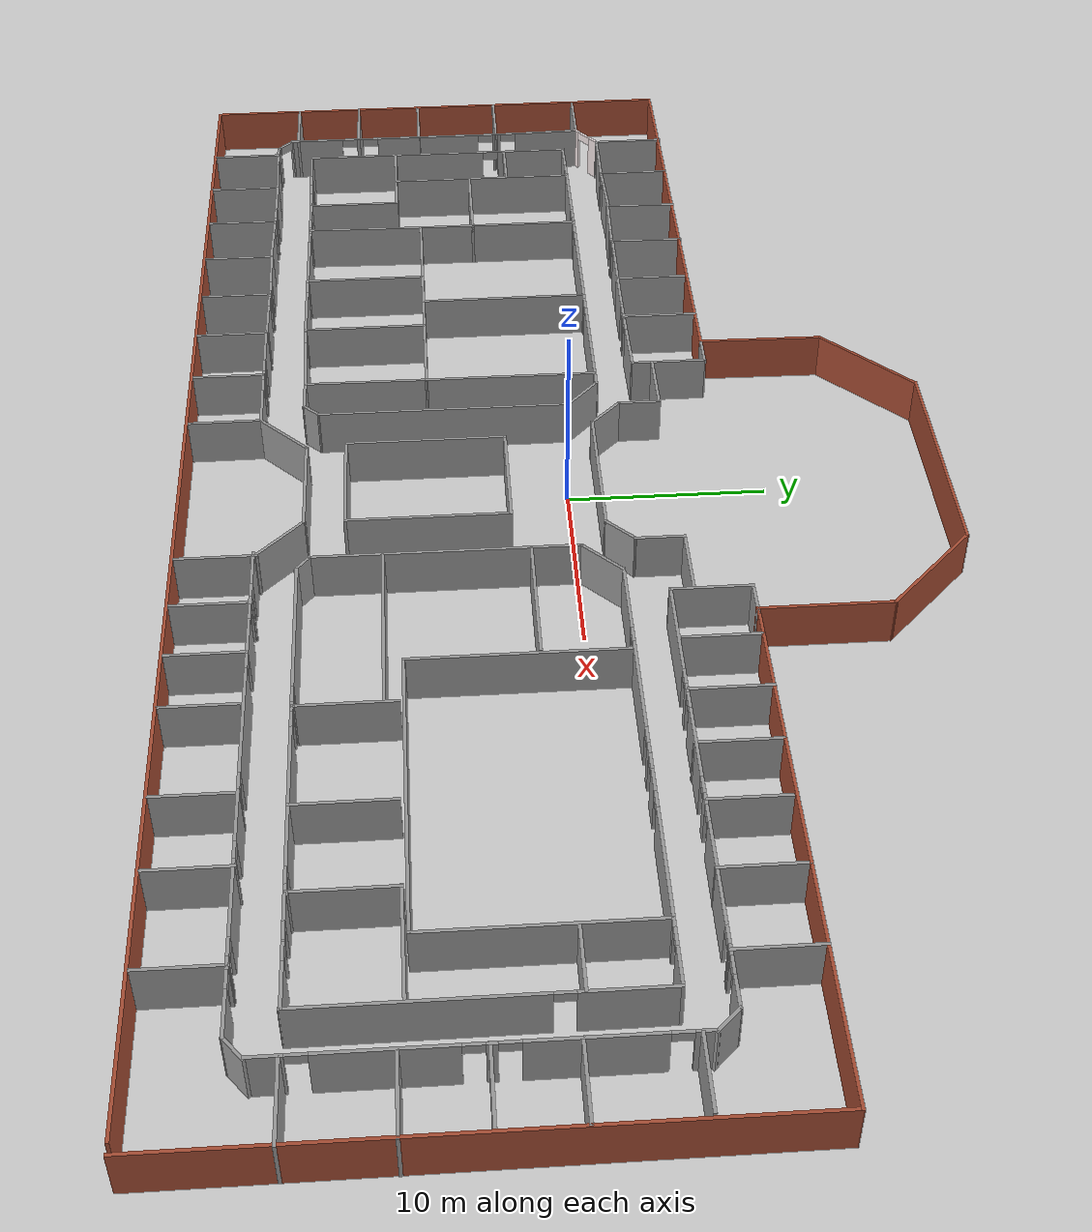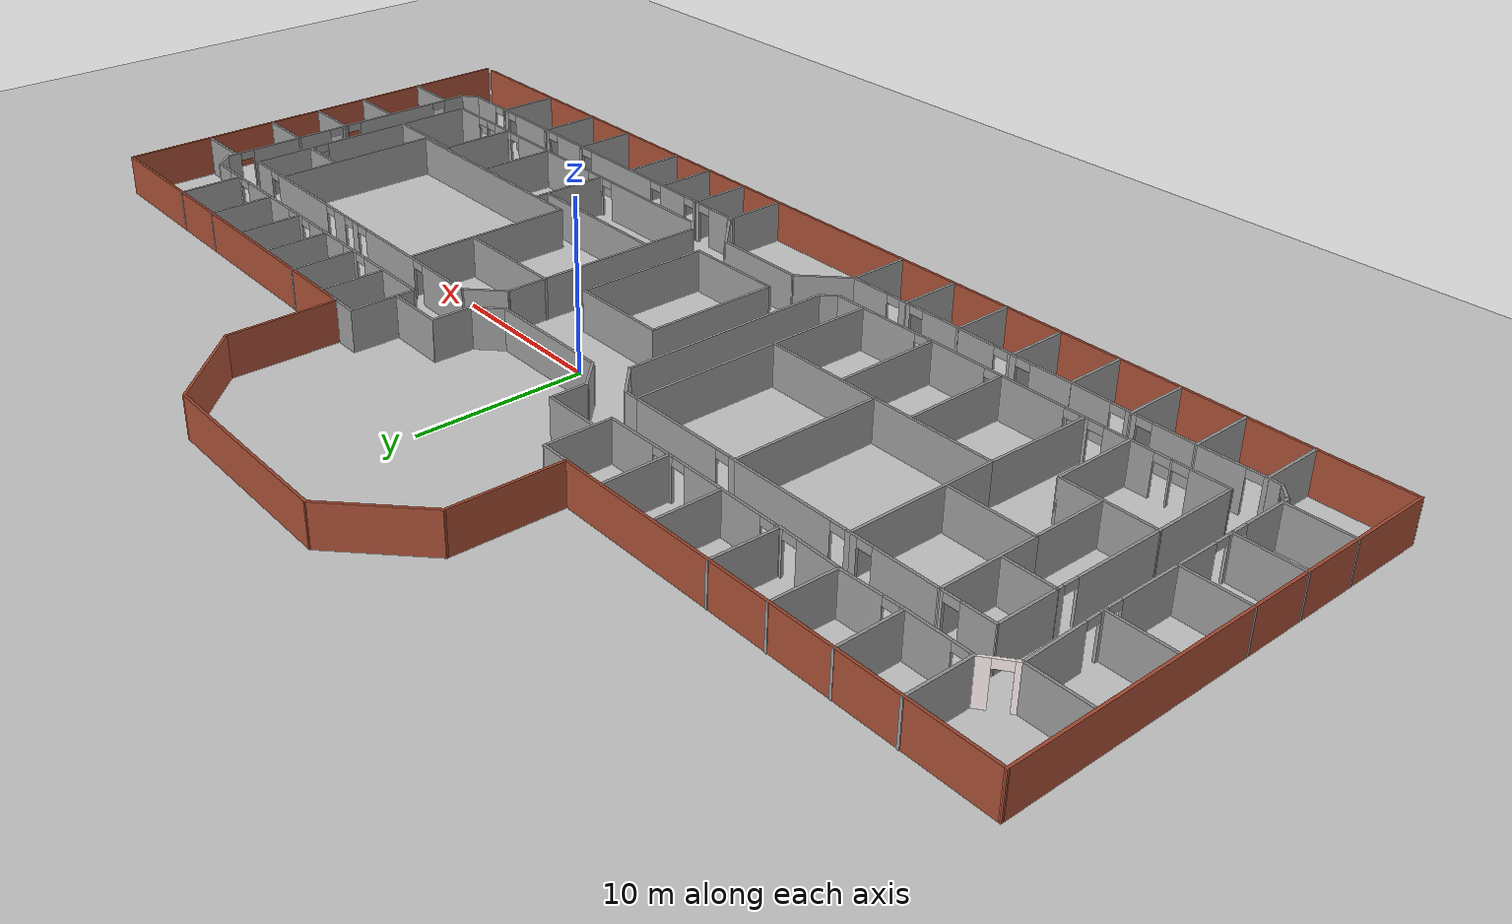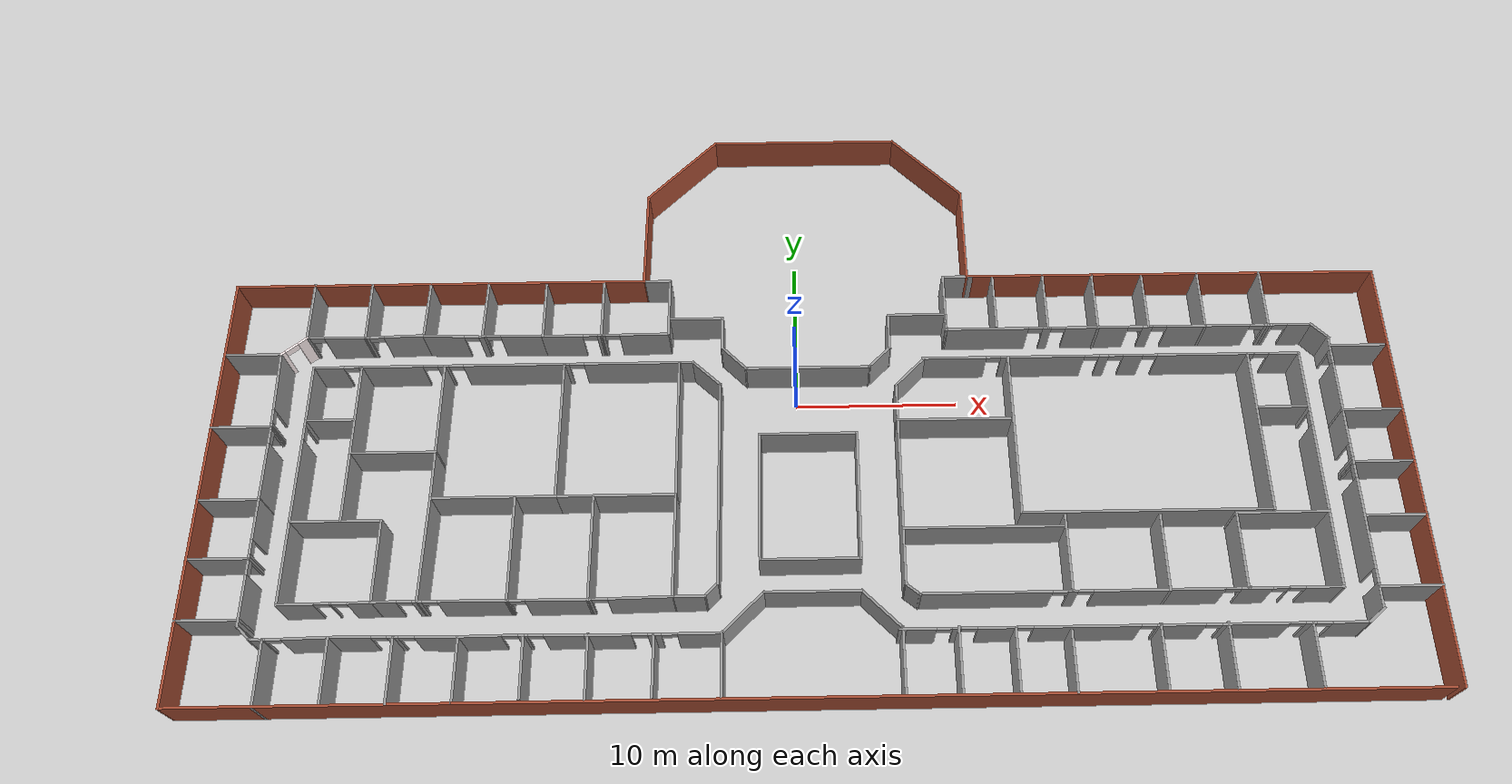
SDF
<sdf version="1.7">
 <world name="default">
  <light name="sun" type="directional">
   <pose>0 0 10 0 -0 0</pose>
   <diffuse>0.8 0.8 0.8 1</diffuse>
   <specular>0.2 0.2 0.2 1</specular>
   <attenuation>
    <range>1000</range>
    <constant>0.9</constant>
    <linear>0.01</linear>
    <quadratic>0.001</quadratic>
   </attenuation>
   <direction>-0.5 0.1 -0.9</direction>
   <spot><inner_angle>0</inner_angle><outer_angle>0</outer_angle><falloff>0</falloff></spot>
  </light>
  <model name="ground_plane">
   <static>1</static>
   <link name="link">
    <collision name="collision">
     <geometry><plane><normal>0 0 1</normal><size>100 100</size></plane></geometry>
     <surface>
      <contact><collide_bitmask>65535</collide_bitmask></contact>
      <friction><ode><mu>100</mu><mu2>50</mu2></ode></friction>
     </surface>
    </collision>
    <visual name="visual">
     <cast_shadows>0</cast_shadows>
     <geometry><plane><normal>0 0 1</normal><size>100 100</size></plane></geometry>
     <material>
      <script><uri>file://media/materials/scripts/gazebo.material</uri><name>Gazebo/Grey</name></script>
     </material>
    </visual>
   </link>
  </model>
  <gravity>0 0 -9.8</gravity>
  <magnetic_field>6e-06 2.3e-05 -4.2e-05</magnetic_field>
  <atmosphere type="adiabatic"/>
  <physics type="ode">
   <max_step_size>0.001</max_step_size>
   <real_time_factor>1</real_time_factor>
   <real_time_update_rate>1000</real_time_update_rate>
  </physics>
  <scene><ambient>0.4 0.4 0.4 1</ambient><background>0.7 0.7 0.7 1</background><shadows>1</shadows></scene>
  <spherical_coordinates>
   <surface_model>EARTH_WGS84</surface_model>
   <latitude_deg>0</latitude_deg>
   <longitude_deg>0</longitude_deg>
   <elevation>0</elevation>
   <heading_deg>0</heading_deg>
  </spherical_coordinates>
  <model name="OEC_2F_B">
   <pose>0.733156 -0.285133 0 0 -0 0</pose>
   <link name="Wall_101">
    <pose>-18.3822 4.28827 0 0 -0 3.12969</pose>
    <visual name="Wall_101_Visual_0">
     <pose>-0.61431 0 1.25 0 -0 0</pose>
     <geometry><box><size>2.68761 0.15 2.5</size></box></geometry>
     <material>
      <script><uri>file://media/materials/scripts/gazebo.material</uri><name>Gazebo/Grey</name></script>
      <ambient>1 1 1 1</ambient>
     </material>
     <meta><layer>0</layer></meta>
    </visual>
    <collision name="Wall_101_Collision_0">
     <geometry><box><size>2.68761 0.15 2.5</size></box></geometry>
     <pose>-0.61431 0 1.25 0 -0 0</pose>
    </collision>
    <visual name="Wall_101_Visual_1">
     <pose>1.7938 0 1.25 0 -0 0</pose>
     <geometry><box><size>0.328619 0.15 2.5</size></box></geometry>
     <material>
      <script><uri>file://media/materials/scripts/gazebo.material</uri><name>Gazebo/Grey</name></script>
      <ambient>1 1 1 1</ambient>
     </material>
     <meta><layer>0</layer></meta>
    </visual>
    <collision name="Wall_101_Collision_1">
     <geometry><box><size>0.328619 0.15 2.5</size></box></geometry>
     <pose>1.7938 0 1.25 0 -0 0</pose>
    </collision>
    <visual name="Wall_101_Visual_2">
     <pose>1.17949 0 2.25 0 -0 0</pose>
     <geometry><box><size>0.9 0.15 0.5</size></box></geometry>
     <material>
      <script><uri>file://media/materials/scripts/gazebo.material</uri><name>Gazebo/Grey</name></script>
      <ambient>1 1 1 1</ambient>
     </material>
     <meta><layer>0</layer></meta>
    </visual>
    <collision name="Wall_101_Collision_2">
     <geometry><box><size>0.9 0.15 0.5</size></box></geometry>
     <pose>1.17949 0 2.25 0 -0 0</pose>
    </collision>
   </link>
   <link name="Wall_102">
    <pose>-22.0485 4.31707 0 0 -0 3.11269</pose>
    <visual name="Wall_102_Visual_0">
     <pose>-1.73863 0 1.25 0 -0 0</pose>
     <geometry><box><size>0.333949 0.15 2.5</size></box></geometry>
     <material>
      <script><uri>file://media/materials/scripts/gazebo.material</uri><name>Gazebo/Grey</name></script>
      <ambient>1 1 1 1</ambient>
     </material>
     <meta><layer>0</layer></meta>
    </visual>
    <collision name="Wall_102_Collision_0">
     <geometry><box><size>0.333949 0.15 2.5</size></box></geometry>
     <pose>-1.73863 0 1.25 0 -0 0</pose>
    </collision>
    <visual name="Wall_102_Visual_1">
     <pose>0.616975 0 1.25 0 -0 0</pose>
     <geometry><box><size>2.57727 0.15 2.5</size></box></geometry>
     <material>
      <script><uri>file://media/materials/scripts/gazebo.material</uri><name>Gazebo/Grey</name></script>
      <ambient>1 1 1 1</ambient>
     </material>
     <meta><layer>0</layer></meta>
    </visual>
    <collision name="Wall_102_Collision_1">
     <geometry><box><size>2.57727 0.15 2.5</size></box></geometry>
     <pose>0.616975 0 1.25 0 -0 0</pose>
    </collision>
    <visual name="Wall_102_Visual_2">
     <pose>-1.12166 0 2.25 0 -0 0</pose>
     <geometry><box><size>0.9 0.15 0.5</size></box></geometry>
     <material>
      <script><uri>file://media/materials/scripts/gazebo.material</uri><name>Gazebo/Grey</name></script>
      <ambient>1 1 1 1</ambient>
     </material>
     <meta><layer>0</layer></meta>
    </visual>
    <collision name="Wall_102_Collision_2">
     <geometry><box><size>0.9 0.15 0.5</size></box></geometry>
     <pose>-1.12166 0 2.25 0 -0 0</pose>
    </collision>
   </link>
   <link name="Wall_104">
    <pose>-25.7323 4.36122 0 0 -0 -3.11102</pose>
    <visual name="Wall_104_Visual_0">
     <pose>-0.610442 0 1.25 0 -0 0</pose>
     <geometry><box><size>2.54565 0.15 2.5</size></box></geometry>
     <material>
      <script><uri>file://media/materials/scripts/gazebo.material</uri><name>Gazebo/Grey</name></script>
      <ambient>1 1 1 1</ambient>
     </material>
     <meta><layer>0</layer></meta>
    </visual>
    <collision name="Wall_104_Collision_0">
     <geometry><box><size>2.54565 0.15 2.5</size></box></geometry>
     <pose>-0.610442 0 1.25 0 -0 0</pose>
    </collision>
    <visual name="Wall_104_Visual_1">
     <pose>1.72283 0 1.25 0 -0 0</pose>
     <geometry><box><size>0.320884 0.15 2.5</size></box></geometry>
     <material>
      <script><uri>file://media/materials/scripts/gazebo.material</uri><name>Gazebo/Grey</name></script>
      <ambient>1 1 1 1</ambient>
     </material>
     <meta><layer>0</layer></meta>
    </visual>
    <collision name="Wall_104_Collision_1">
     <geometry><box><size>0.320884 0.15 2.5</size></box></geometry>
     <pose>1.72283 0 1.25 0 -0 0</pose>
    </collision>
    <visual name="Wall_104_Visual_2">
     <pose>1.11238 0 2.25 0 -0 0</pose>
     <geometry><box><size>0.9 0.15 0.5</size></box></geometry>
     <material>
      <script><uri>file://media/materials/scripts/gazebo.material</uri><name>Gazebo/Grey</name></script>
      <ambient>1 1 1 1</ambient>
     </material>
     <meta><layer>0</layer></meta>
    </visual>
    <collision name="Wall_104_Collision_2">
     <geometry><box><size>0.9 0.15 0.5</size></box></geometry>
     <pose>1.11238 0 2.25 0 -0 0</pose>
    </collision>
   </link>
   <link name="Wall_105">
    <pose>-29.3587 4.32345 0 0 -0 3.13198</pose>
    <visual name="Wall_105_Visual_0">
     <pose>-0.586662 0 1.25 0 -0 0</pose>
     <geometry><box><size>2.61478 0.15 2.5</size></box></geometry>
     <material>
      <script><uri>file://media/materials/scripts/gazebo.material</uri><name>Gazebo/Grey</name></script>
      <ambient>1 1 1 1</ambient>
     </material>
     <meta><layer>0</layer></meta>
    </visual>
    <collision name="Wall_105_Collision_0">
     <geometry><box><size>2.61478 0.15 2.5</size></box></geometry>
     <pose>-0.586662 0 1.25 0 -0 0</pose>
    </collision>
    <visual name="Wall_105_Visual_1">
     <pose>1.75739 0 1.25 0 -0 0</pose>
     <geometry><box><size>0.273323 0.15 2.5</size></box></geometry>
     <material>
      <script><uri>file://media/materials/scripts/gazebo.material</uri><name>Gazebo/Grey</name></script>
      <ambient>1 1 1 1</ambient>
     </material>
     <meta><layer>0</layer></meta>
    </visual>
    <collision name="Wall_105_Collision_1">
     <geometry><box><size>0.273323 0.15 2.5</size></box></geometry>
     <pose>1.75739 0 1.25 0 -0 0</pose>
    </collision>
    <visual name="Wall_105_Visual_2">
     <pose>1.17073 0 2.25 0 -0 0</pose>
     <geometry><box><size>0.9 0.15 0.5</size></box></geometry>
     <material>
      <script><uri>file://media/materials/scripts/gazebo.material</uri><name>Gazebo/Grey</name></script>
      <ambient>1 1 1 1</ambient>
     </material>
     <meta><layer>0</layer></meta>
    </visual>
    <collision name="Wall_105_Collision_2">
     <geometry><box><size>0.9 0.15 0.5</size></box></geometry>
     <pose>1.17073 0 2.25 0 -0 0</pose>
    </collision>
   </link>
   <link name="Wall_107">
    <pose>-31.8931 3.77384 0 0 -0 -2.47133</pose>
    <visual name="Wall_107_Visual_0">
     <pose>-0.62608 0 1.25 0 -0 0</pose>
     <geometry><box><size>0.723685 0.15 2.5</size></box></geometry>
     <material>
      <script><uri>file://media/materials/scripts/gazebo.material</uri><name>Gazebo/Grey</name></script>
      <ambient>0.960784 0.905882 0.905882 1</ambient>
     </material>
     <meta><layer>0</layer></meta>
    </visual>
    <collision name="Wall_107_Collision_0">
     <geometry><box><size>0.723685 0.15 2.5</size></box></geometry>
     <pose>-0.62608 0 1.25 0 -0 0</pose>
    </collision>
    <visual name="Wall_107_Visual_1">
     <pose>0.811843 0 1.25 0 -0 0</pose>
     <geometry><box><size>0.352159 0.15 2.5</size></box></geometry>
     <material>
      <script><uri>file://media/materials/scripts/gazebo.material</uri><name>Gazebo/Grey</name></script>
      <ambient>0.960784 0.905882 0.905882 1</ambient>
     </material>
     <meta><layer>0</layer></meta>
    </visual>
    <collision name="Wall_107_Collision_1">
     <geometry><box><size>0.352159 0.15 2.5</size></box></geometry>
     <pose>0.811843 0 1.25 0 -0 0</pose>
    </collision>
    <visual name="Wall_107_Visual_2">
     <pose>0.185763 0 2.25 0 -0 0</pose>
     <geometry><box><size>0.9 0.15 0.5</size></box></geometry>
     <material>
      <script><uri>file://media/materials/scripts/gazebo.material</uri><name>Gazebo/Grey</name></script>
      <ambient>0.960784 0.905882 0.905882 1</ambient>
     </material>
     <meta><layer>0</layer></meta>
    </visual>
    <collision name="Wall_107_Collision_2">
     <geometry><box><size>0.9 0.15 0.5</size></box></geometry>
     <pose>0.185763 0 2.25 0 -0 0</pose>
    </collision>
   </link>
   <link name="Wall_109">
    <collision name="Wall_109_Collision">
     <geometry><box><size>1 0.15 2.5</size></box></geometry>
     <pose>0 0 1.25 0 -0 0</pose>
    </collision>
    <visual name="Wall_109_Visual">
     <pose>0 0 1.25 0 -0 0</pose>
     <geometry><box><size>1 0.15 2.5</size></box></geometry>
     <material>
      <script><uri>file://media/materials/scripts/gazebo.material</uri><name>Gazebo/Grey</name></script>
      <ambient>1 1 1 1</ambient>
     </material>
     <meta><layer>0</layer></meta>
    </visual>
    <pose>-7.50932 2.23651 0 0 -0 3.14159</pose>
   </link>
   <link name="Wall_110">
    <pose>-11.4843 2.23651 0 0 -0 3.14159</pose>
    <visual name="Wall_110_Visual_0">
     <pose>-0.645977 0 1.25 0 -0 0</pose>
     <geometry><box><size>5.95805 0.15 2.5</size></box></geometry>
     <material>
      <script><uri>file://media/materials/scripts/gazebo.material</uri><name>Gazebo/Grey</name></script>
      <ambient>1 1 1 1</ambient>
     </material>
     <meta><layer>0</layer></meta>
    </visual>
    <collision name="Wall_110_Collision_0">
     <geometry><box><size>5.95805 0.15 2.5</size></box></geometry>
     <pose>-0.645977 0 1.25 0 -0 0</pose>
    </collision>
    <visual name="Wall_110_Visual_1">
     <pose>3.42902 0 1.25 0 -0 0</pose>
     <geometry><box><size>0.391954 0.15 2.5</size></box></geometry>
     <material>
      <script><uri>file://media/materials/scripts/gazebo.material</uri><name>Gazebo/Grey</name></script>
      <ambient>1 1 1 1</ambient>
     </material>
     <meta><layer>0</layer></meta>
    </visual>
    <collision name="Wall_110_Collision_1">
     <geometry><box><size>0.391954 0.15 2.5</size></box></geometry>
     <pose>3.42902 0 1.25 0 -0 0</pose>
    </collision>
    <visual name="Wall_110_Visual_2">
     <pose>2.78305 0 2.25 0 -0 0</pose>
     <geometry><box><size>0.9 0.15 0.5</size></box></geometry>
     <material>
      <script><uri>file://media/materials/scripts/gazebo.material</uri><name>Gazebo/Grey</name></script>
      <ambient>1 1 1 1</ambient>
     </material>
     <meta><layer>0</layer></meta>
    </visual>
    <collision name="Wall_110_Collision_2">
     <geometry><box><size>0.9 0.15 0.5</size></box></geometry>
     <pose>2.78305 0 2.25 0 -0 0</pose>
    </collision>
   </link>
   <link name="Wall_111">
    <pose>-18.7093 2.23651 0 0 -0 3.14159</pose>
    <visual name="Wall_111_Visual_0">
     <pose>-0.604339 0 1.25 0 -0 0</pose>
     <geometry><box><size>6.29132 0.15 2.5</size></box></geometry>
     <material>
      <script><uri>file://media/materials/scripts/gazebo.material</uri><name>Gazebo/Grey</name></script>
      <ambient>1 1 1 1</ambient>
     </material>
     <meta><layer>0</layer></meta>
    </visual>
    <collision name="Wall_111_Collision_0">
     <geometry><box><size>6.29132 0.15 2.5</size></box></geometry>
     <pose>-0.604339 0 1.25 0 -0 0</pose>
    </collision>
    <visual name="Wall_111_Visual_1">
     <pose>3.59566 0 1.25 0 -0 0</pose>
     <geometry><box><size>0.308678 0.15 2.5</size></box></geometry>
     <material>
      <script><uri>file://media/materials/scripts/gazebo.material</uri><name>Gazebo/Grey</name></script>
      <ambient>1 1 1 1</ambient>
     </material>
     <meta><layer>0</layer></meta>
    </visual>
    <collision name="Wall_111_Collision_1">
     <geometry><box><size>0.308678 0.15 2.5</size></box></geometry>
     <pose>3.59566 0 1.25 0 -0 0</pose>
    </collision>
    <visual name="Wall_111_Visual_2">
     <pose>2.99132 0 2.25 0 -0 0</pose>
     <geometry><box><size>0.9 0.15 0.5</size></box></geometry>
     <material>
      <script><uri>file://media/materials/scripts/gazebo.material</uri><name>Gazebo/Grey</name></script>
      <ambient>1 1 1 1</ambient>
     </material>
     <meta><layer>0</layer></meta>
    </visual>
    <collision name="Wall_111_Collision_2">
     <geometry><box><size>0.9 0.15 0.5</size></box></geometry>
     <pose>2.99132 0 2.25 0 -0 0</pose>
    </collision>
   </link>
   <link name="Wall_113">
    <pose>-24.9343 2.23651 0 0 -0 3.14159</pose>
    <visual name="Wall_113_Visual_0">
     <pose>-2.35854 0 1.25 0 -0 0</pose>
     <geometry><box><size>0.532918 0.15 2.5</size></box></geometry>
     <material>
      <script><uri>file://media/materials/scripts/gazebo.material</uri><name>Gazebo/Grey</name></script>
      <ambient>1 1 1 1</ambient>
     </material>
     <meta><layer>0</layer></meta>
    </visual>
    <collision name="Wall_113_Collision_0">
     <geometry><box><size>0.532918 0.15 2.5</size></box></geometry>
     <pose>-2.35854 0 1.25 0 -0 0</pose>
    </collision>
    <visual name="Wall_113_Visual_1">
     <pose>0.716459 0 1.25 0 -0 0</pose>
     <geometry><box><size>3.81708 0.15 2.5</size></box></geometry>
     <material>
      <script><uri>file://media/materials/scripts/gazebo.material</uri><name>Gazebo/Grey</name></script>
      <ambient>1 1 1 1</ambient>
     </material>
     <meta><layer>0</layer></meta>
    </visual>
    <collision name="Wall_113_Collision_1">
     <geometry><box><size>3.81708 0.15 2.5</size></box></geometry>
     <pose>0.716459 0 1.25 0 -0 0</pose>
    </collision>
    <visual name="Wall_113_Visual_2">
     <pose>-1.64208 0 2.25 0 -0 0</pose>
     <geometry><box><size>0.9 0.15 0.5</size></box></geometry>
     <material>
      <script><uri>file://media/materials/scripts/gazebo.material</uri><name>Gazebo/Grey</name></script>
      <ambient>1 1 1 1</ambient>
     </material>
     <meta><layer>0</layer></meta>
    </visual>
    <collision name="Wall_113_Collision_2">
     <geometry><box><size>0.9 0.15 0.5</size></box></geometry>
     <pose>-1.64208 0 2.25 0 -0 0</pose>
    </collision>
   </link>
   <link name="Wall_115">
    <pose>-28.9692 2.22462 0 0 -0 -3.13359</pose>
    <visual name="Wall_115_Visual_0">
     <pose>-1.41288 0 1.25 0 -0 0</pose>
     <geometry><box><size>0.294093 0.15 2.5</size></box></geometry>
     <material>
      <script><uri>file://media/materials/scripts/gazebo.material</uri><name>Gazebo/Grey</name></script>
      <ambient>1 1 1 1</ambient>
     </material>
     <meta><layer>0</layer></meta>
    </visual>
    <collision name="Wall_115_Collision_0">
     <geometry><box><size>0.294093 0.15 2.5</size></box></geometry>
     <pose>-1.41288 0 1.25 0 -0 0</pose>
    </collision>
    <visual name="Wall_115_Visual_1">
     <pose>0.597047 0 1.25 0 -0 0</pose>
     <geometry><box><size>1.92576 0.15 2.5</size></box></geometry>
     <material>
      <script><uri>file://media/materials/scripts/gazebo.material</uri><name>Gazebo/Grey</name></script>
      <ambient>1 1 1 1</ambient>
     </material>
     <meta><layer>0</layer></meta>
    </visual>
    <collision name="Wall_115_Collision_1">
     <geometry><box><size>1.92576 0.15 2.5</size></box></geometry>
     <pose>0.597047 0 1.25 0 -0 0</pose>
    </collision>
    <visual name="Wall_115_Visual_2">
     <pose>-0.815835 0 2.25 0 -0 0</pose>
     <geometry><box><size>0.9 0.15 0.5</size></box></geometry>
     <material>
      <script><uri>file://media/materials/scripts/gazebo.material</uri><name>Gazebo/Grey</name></script>
      <ambient>1 1 1 1</ambient>
     </material>
     <meta><layer>0</layer></meta>
    </visual>
    <collision name="Wall_115_Collision_2">
     <geometry><box><size>0.9 0.15 0.5</size></box></geometry>
     <pose>-0.815835 0 2.25 0 -0 0</pose>
    </collision>
   </link>
   <link name="Wall_118">
    <collision name="Wall_118_Collision">
     <geometry><box><size>9 0.15 2.5</size></box></geometry>
     <pose>0 0 1.25 0 -0 0</pose>
    </collision>
    <visual name="Wall_118_Visual">
     <pose>0 0 1.25 0 -0 0</pose>
     <geometry><box><size>9 0.15 2.5</size></box></geometry>
     <material>
      <script><uri>file://media/materials/scripts/gazebo.material</uri><name>Gazebo/Grey</name></script>
      <ambient>1 1 1 1</ambient>
     </material>
     <meta><layer>0</layer></meta>
    </visual>
    <pose>-7.93432 -2.1885 0 0 -0 -1.5708</pose>
   </link>
   <link name="Wall_120">
    <collision name="Wall_120_Collision">
     <geometry><box><size>9 0.15 2.5</size></box></geometry>
     <pose>0 0 1.25 0 -0 0</pose>
    </collision>
    <visual name="Wall_120_Visual">
     <pose>0 0 1.25 0 -0 0</pose>
     <geometry><box><size>9 0.15 2.5</size></box></geometry>
     <material>
      <script><uri>file://media/materials/scripts/gazebo.material</uri><name>Gazebo/Grey</name></script>
      <ambient>1 1 1 1</ambient>
     </material>
     <meta><layer>0</layer></meta>
    </visual>
    <pose>-15.0343 -2.1885 0 0 -0 -1.5708</pose>
   </link>
   <link name="Wall_122">
    <collision name="Wall_122_Collision">
     <geometry><box><size>9 0.15 2.5</size></box></geometry>
     <pose>0 0 1.25 0 -0 0</pose>
    </collision>
    <visual name="Wall_122_Visual">
     <pose>0 0 1.25 0 -0 0</pose>
     <geometry><box><size>9 0.15 2.5</size></box></geometry>
     <material>
      <script><uri>file://media/materials/scripts/gazebo.material</uri><name>Gazebo/Grey</name></script>
      <ambient>1 1 1 1</ambient>
     </material>
     <meta><layer>0</layer></meta>
    </visual>
    <pose>-22.3843 -2.1885 0 0 -0 -1.5708</pose>
   </link>
   <link name="Wall_124">
    <collision name="Wall_124_Collision">
     <geometry><box><size>6 0.15 2.5</size></box></geometry>
     <pose>0 0 1.25 0 -0 0</pose>
    </collision>
    <visual name="Wall_124_Visual">
     <pose>0 0 1.25 0 -0 0</pose>
     <geometry><box><size>6 0.15 2.5</size></box></geometry>
     <material>
      <script><uri>file://media/materials/scripts/gazebo.material</uri><name>Gazebo/Grey</name></script>
      <ambient>1 1 1 1</ambient>
     </material>
     <meta><layer>0</layer></meta>
    </visual>
    <pose>-27.4843 -0.688495 0 0 -0 -1.5708</pose>
   </link>
   <link name="Wall_127">
    <collision name="Wall_127_Collision">
     <geometry><box><size>7.25 0.15 2.5</size></box></geometry>
     <pose>0 0 1.25 0 -0 0</pose>
    </collision>
    <visual name="Wall_127_Visual">
     <pose>0 0 1.25 0 -0 0</pose>
     <geometry><box><size>7.25 0.15 2.5</size></box></geometry>
     <material>
      <script><uri>file://media/materials/scripts/gazebo.material</uri><name>Gazebo/Grey</name></script>
      <ambient>1 1 1 1</ambient>
     </material>
     <meta><layer>0</layer></meta>
    </visual>
    <pose>-11.4843 -6.6135 0 0 -0 3.14159</pose>
   </link>
   <link name="Wall_128">
    <collision name="Wall_128_Collision">
     <geometry><box><size>7.5 0.15 2.5</size></box></geometry>
     <pose>0 0 1.25 0 -0 0</pose>
    </collision>
    <visual name="Wall_128_Visual">
     <pose>0 0 1.25 0 -0 0</pose>
     <geometry><box><size>7.5 0.15 2.5</size></box></geometry>
     <material>
      <script><uri>file://media/materials/scripts/gazebo.material</uri><name>Gazebo/Grey</name></script>
      <ambient>1 1 1 1</ambient>
     </material>
     <meta><layer>0</layer></meta>
    </visual>
    <pose>-18.7093 -6.6135 0 0 -0 3.14159</pose>
   </link>
   <link name="Wall_130">
    <collision name="Wall_130_Collision">
     <geometry><box><size>5.25 0.15 2.5</size></box></geometry>
     <pose>0 0 1.25 0 -0 0</pose>
    </collision>
    <visual name="Wall_130_Visual">
     <pose>0 0 1.25 0 -0 0</pose>
     <geometry><box><size>5.25 0.15 2.5</size></box></geometry>
     <material>
      <script><uri>file://media/materials/scripts/gazebo.material</uri><name>Gazebo/Grey</name></script>
      <ambient>1 1 1 1</ambient>
     </material>
     <meta><layer>0</layer></meta>
    </visual>
    <pose>-24.9343 -3.61349 0 0 -0 0</pose>
   </link>
   <link name="Wall_132">
    <pose>-32.5386 0.717956 0 0 -0 -1.54269</pose>
    <visual name="Wall_132_Visual_0">
     <pose>-0.617333 0 1.25 0 -0 0</pose>
     <geometry><box><size>3.89487 0.15 2.5</size></box></geometry>
     <material>
      <script><uri>file://media/materials/scripts/gazebo.material</uri><name>Gazebo/Grey</name></script>
      <ambient>1 1 1 1</ambient>
     </material>
     <meta><layer>0</layer></meta>
    </visual>
    <collision name="Wall_132_Collision_0">
     <geometry><box><size>3.89487 0.15 2.5</size></box></geometry>
     <pose>-0.617333 0 1.25 0 -0 0</pose>
    </collision>
    <visual name="Wall_132_Visual_1">
     <pose>2.39744 0 1.25 0 -0 0</pose>
     <geometry><box><size>0.334666 0.15 2.5</size></box></geometry>
     <material>
      <script><uri>file://media/materials/scripts/gazebo.material</uri><name>Gazebo/Grey</name></script>
      <ambient>1 1 1 1</ambient>
     </material>
     <meta><layer>0</layer></meta>
    </visual>
    <collision name="Wall_132_Collision_1">
     <geometry><box><size>0.334666 0.15 2.5</size></box></geometry>
     <pose>2.39744 0 1.25 0 -0 0</pose>
    </collision>
    <visual name="Wall_132_Visual_2">
     <pose>1.7801 0 2.25 0 -0 0</pose>
     <geometry><box><size>0.9 0.15 0.5</size></box></geometry>
     <material>
      <script><uri>file://media/materials/scripts/gazebo.material</uri><name>Gazebo/Grey</name></script>
      <ambient>1 1 1 1</ambient>
     </material>
     <meta><layer>0</layer></meta>
    </visual>
    <collision name="Wall_132_Collision_2">
     <geometry><box><size>0.9 0.15 0.5</size></box></geometry>
     <pose>1.7801 0 2.25 0 -0 0</pose>
    </collision>
   </link>
   <link name="Wall_134">
    <pose>-32.4686 -4.16702 0 0 -0 -1.5708</pose>
    <visual name="Wall_134_Visual_0">
     <pose>-2.33578 0 1.25 0 -0 0</pose>
     <geometry><box><size>0.270827 0.15 2.5</size></box></geometry>
     <material>
      <script><uri>file://media/materials/scripts/gazebo.material</uri><name>Gazebo/Grey</name></script>
      <ambient>1 1 1 1</ambient>
     </material>
     <meta><layer>0</layer></meta>
    </visual>
    <collision name="Wall_134_Collision_0">
     <geometry><box><size>0.270827 0.15 2.5</size></box></geometry>
     <pose>-2.33578 0 1.25 0 -0 0</pose>
    </collision>
    <visual name="Wall_134_Visual_1">
     <pose>0.585414 0 1.25 0 -0 0</pose>
     <geometry><box><size>3.77156 0.15 2.5</size></box></geometry>
     <material>
      <script><uri>file://media/materials/scripts/gazebo.material</uri><name>Gazebo/Grey</name></script>
      <ambient>1 1 1 1</ambient>
     </material>
     <meta><layer>0</layer></meta>
    </visual>
    <collision name="Wall_134_Collision_1">
     <geometry><box><size>3.77156 0.15 2.5</size></box></geometry>
     <pose>0.585414 0 1.25 0 -0 0</pose>
    </collision>
    <visual name="Wall_134_Visual_2">
     <pose>-1.75037 0 2.25 0 -0 0</pose>
     <geometry><box><size>0.9 0.15 0.5</size></box></geometry>
     <material>
      <script><uri>file://media/materials/scripts/gazebo.material</uri><name>Gazebo/Grey</name></script>
      <ambient>1 1 1 1</ambient>
     </material>
     <meta><layer>0</layer></meta>
    </visual>
    <collision name="Wall_134_Collision_2">
     <geometry><box><size>0.9 0.15 0.5</size></box></geometry>
     <pose>-1.75037 0 2.25 0 -0 0</pose>
    </collision>
   </link>
   <link name="Wall_135">
    <pose>-32.4686 -8.39202 0 0 -0 -1.5708</pose>
    <visual name="Wall_135_Visual_0">
     <pose>-0.617157 0 1.25 0 -0 0</pose>
     <geometry><box><size>2.5733 0.15 2.5</size></box></geometry>
     <material>
      <script><uri>file://media/materials/scripts/gazebo.material</uri><name>Gazebo/Grey</name></script>
      <ambient>1 1 1 1</ambient>
     </material>
     <meta><layer>0</layer></meta>
    </visual>
    <collision name="Wall_135_Collision_0">
     <geometry><box><size>2.5733 0.15 2.5</size></box></geometry>
     <pose>-0.617157 0 1.25 0 -0 0</pose>
    </collision>
    <visual name="Wall_135_Visual_1">
     <pose>1.73665 0 1.25 0 -0 0</pose>
     <geometry><box><size>0.334313 0.15 2.5</size></box></geometry>
     <material>
      <script><uri>file://media/materials/scripts/gazebo.material</uri><name>Gazebo/Grey</name></script>
      <ambient>1 1 1 1</ambient>
     </material>
     <meta><layer>0</layer></meta>
    </visual>
    <collision name="Wall_135_Collision_1">
     <geometry><box><size>0.334313 0.15 2.5</size></box></geometry>
     <pose>1.73665 0 1.25 0 -0 0</pose>
    </collision>
    <visual name="Wall_135_Visual_2">
     <pose>1.11949 0 2.25 0 -0 0</pose>
     <geometry><box><size>0.9 0.15 0.5</size></box></geometry>
     <material>
      <script><uri>file://media/materials/scripts/gazebo.material</uri><name>Gazebo/Grey</name></script>
      <ambient>1 1 1 1</ambient>
     </material>
     <meta><layer>0</layer></meta>
    </visual>
    <collision name="Wall_135_Collision_2">
     <geometry><box><size>0.9 0.15 0.5</size></box></geometry>
     <pose>1.11949 0 2.25 0 -0 0</pose>
    </collision>
   </link>
   <link name="Wall_137">
    <pose>-32.4686 -12.2458 0 0 -0 -1.5708</pose>
    <visual name="Wall_137_Visual_0">
     <pose>-2.00493 0 1.25 0 -0 0</pose>
     <geometry><box><size>0.190132 0.15 2.5</size></box></geometry>
     <material>
      <script><uri>file://media/materials/scripts/gazebo.material</uri><name>Gazebo/Grey</name></script>
      <ambient>1 1 1 1</ambient>
     </material>
     <meta><layer>0</layer></meta>
    </visual>
    <collision name="Wall_137_Collision_0">
     <geometry><box><size>0.190132 0.15 2.5</size></box></geometry>
     <pose>-2.00493 0 1.25 0 -0 0</pose>
    </collision>
    <visual name="Wall_137_Visual_1">
     <pose>0.545066 0 1.25 0 -0 0</pose>
     <geometry><box><size>3.10987 0.15 2.5</size></box></geometry>
     <material>
      <script><uri>file://media/materials/scripts/gazebo.material</uri><name>Gazebo/Grey</name></script>
      <ambient>1 1 1 1</ambient>
     </material>
     <meta><layer>0</layer></meta>
    </visual>
    <collision name="Wall_137_Collision_1">
     <geometry><box><size>3.10987 0.15 2.5</size></box></geometry>
     <pose>0.545066 0 1.25 0 -0 0</pose>
    </collision>
    <visual name="Wall_137_Visual_2">
     <pose>-1.45987 0 2.25 0 -0 0</pose>
     <geometry><box><size>0.9 0.15 0.5</size></box></geometry>
     <material>
      <script><uri>file://media/materials/scripts/gazebo.material</uri><name>Gazebo/Grey</name></script>
      <ambient>1 1 1 1</ambient>
     </material>
     <meta><layer>0</layer></meta>
    </visual>
    <collision name="Wall_137_Collision_2">
     <geometry><box><size>0.9 0.15 0.5</size></box></geometry>
     <pose>-1.45987 0 2.25 0 -0 0</pose>
    </collision>
   </link>
   <link name="Wall_139">
    <collision name="Wall_139_Collision">
     <geometry><box><size>3.5 0.15 2.5</size></box></geometry>
     <pose>0 0 1.25 0 -0 0</pose>
    </collision>
    <visual name="Wall_139_Visual">
     <pose>0 0 1.25 0 -0 0</pose>
     <geometry><box><size>3.5 0.15 2.5</size></box></geometry>
     <material>
      <script><uri>file://media/materials/scripts/gazebo.material</uri><name>Gazebo/Grey</name></script>
      <ambient>1 1 1 1</ambient>
     </material>
     <meta><layer>0</layer></meta>
    </visual>
    <pose>-34.2835 3.20674 0 0 -0 3.14159</pose>
   </link>
   <link name="Wall_14">
    <collision name="Wall_14_Collision">
     <geometry><box><size>6.57649 0.15 2.5</size></box></geometry>
     <pose>0 0 1.25 0 -0 0</pose>
    </collision>
    <visual name="Wall_14_Visual">
     <pose>0 0 1.25 0 -0 0</pose>
     <geometry><box><size>6.57649 0.15 2.5</size></box></geometry>
     <material>
      <script><uri>file://media/materials/scripts/gazebo.material</uri><name>Gazebo/Bricks</name></script>
      <ambient>1 1 1 1</ambient>
     </material>
     <meta><layer>0</layer></meta>
    </visual>
    <pose>-10.2885 11.3541 0 0 -0 1.55896</pose>
   </link>
   <link name="Wall_141">
    <collision name="Wall_141_Collision">
     <geometry><box><size>3.75 0.15 2.5</size></box></geometry>
     <pose>0 0 1.25 0 -0 0</pose>
    </collision>
    <visual name="Wall_141_Visual">
     <pose>0 0 1.25 0 -0 0</pose>
     <geometry><box><size>3.75 0.15 2.5</size></box></geometry>
     <material>
      <script><uri>file://media/materials/scripts/gazebo.material</uri><name>Gazebo/Grey</name></script>
      <ambient>1 1 1 1</ambient>
     </material>
     <meta><layer>0</layer></meta>
    </visual>
    <pose>-34.2686 -1.77083 0 0 -0 3.14159</pose>
   </link>
   <link name="Wall_143">
    <collision name="Wall_143_Collision">
     <geometry><box><size>3.75 0.15 2.5</size></box></geometry>
     <pose>0 0 1.25 0 -0 0</pose>
    </collision>
    <visual name="Wall_143_Visual">
     <pose>0 0 1.25 0 -0 0</pose>
     <geometry><box><size>3.75 0.15 2.5</size></box></geometry>
     <material>
      <script><uri>file://media/materials/scripts/gazebo.material</uri><name>Gazebo/Grey</name></script>
      <ambient>1 1 1 1</ambient>
     </material>
     <meta><layer>0</layer></meta>
    </visual>
    <pose>-34.2686 -6.52824 0 0 -0 3.14159</pose>
   </link>
   <link name="Wall_145">
    <collision name="Wall_145_Collision">
     <geometry><box><size>3.75 0.15 2.5</size></box></geometry>
     <pose>0 0 1.25 0 -0 0</pose>
    </collision>
    <visual name="Wall_145_Visual">
     <pose>0 0 1.25 0 -0 0</pose>
     <geometry><box><size>3.75 0.15 2.5</size></box></geometry>
     <material>
      <script><uri>file://media/materials/scripts/gazebo.material</uri><name>Gazebo/Grey</name></script>
      <ambient>1 1 1 1</ambient>
     </material>
     <meta><layer>0</layer></meta>
    </visual>
    <pose>-34.2686 -10.2208 0 0 -0 3.14159</pose>
   </link>
   <link name="Wall_148">
    <collision name="Wall_148_Collision">
     <geometry><box><size>3.75 0.15 2.5</size></box></geometry>
     <pose>0 0 1.25 0 -0 0</pose>
    </collision>
    <visual name="Wall_148_Visual">
     <pose>0 0 1.25 0 -0 0</pose>
     <geometry><box><size>3.75 0.15 2.5</size></box></geometry>
     <material>
      <script><uri>file://media/materials/scripts/gazebo.material</uri><name>Gazebo/Grey</name></script>
      <ambient>1 1 1 1</ambient>
     </material>
     <meta><layer>0</layer></meta>
    </visual>
    <pose>-34.257 -13.9167 0 0 -0 3.14159</pose>
   </link>
   <link name="Wall_15">
    <collision name="Wall_15_Collision">
     <geometry><box><size>6.25 0.15 2.5</size></box></geometry>
     <pose>0 0 1.25 0 -0 0</pose>
    </collision>
    <visual name="Wall_15_Visual">
     <pose>0 0 1.25 0 -0 0</pose>
     <geometry><box><size>6.25 0.15 2.5</size></box></geometry>
     <material>
      <script><uri>file://media/materials/scripts/gazebo.material</uri><name>Gazebo/Bricks</name></script>
      <ambient>1 1 1 1</ambient>
     </material>
     <meta><layer>0</layer></meta>
    </visual>
    <pose>-8.09384 16.7238 0 0 -0 0.785398</pose>
   </link>
   <link name="Wall_150">
    <collision name="Wall_150_Collision">
     <geometry><box><size>3.75 0.15 2.5</size></box></geometry>
     <pose>0 0 1.25 0 -0 0</pose>
    </collision>
    <visual name="Wall_150_Visual">
     <pose>0 0 1.25 0 -0 0</pose>
     <geometry><box><size>3.75 0.15 2.5</size></box></geometry>
     <material>
      <script><uri>file://media/materials/scripts/gazebo.material</uri><name>Gazebo/Grey</name></script>
      <ambient>1 1 1 1</ambient>
     </material>
     <meta><layer>0</layer></meta>
    </visual>
    <pose>-30.4453 0.412732 0 0 -0 -1.56594</pose>
   </link>
   <link name="Wall_151">
    <pose>-30.4453 -4.68727 0 0 -0 -1.57345</pose>
    <visual name="Wall_151_Visual_0">
     <pose>-3.14822 0 1.25 0 -0 0</pose>
     <geometry><box><size>0.453553 0.15 2.5</size></box></geometry>
     <material>
      <script><uri>file://media/materials/scripts/gazebo.material</uri><name>Gazebo/Grey</name></script>
      <ambient>1 1 1 1</ambient>
     </material>
     <meta><layer>0</layer></meta>
    </visual>
    <collision name="Wall_151_Collision_0">
     <geometry><box><size>0.453553 0.15 2.5</size></box></geometry>
     <pose>-3.14822 0 1.25 0 -0 0</pose>
    </collision>
    <visual name="Wall_151_Visual_1">
     <pose>0.676776 0 1.25 0 -0 0</pose>
     <geometry><box><size>5.39645 0.15 2.5</size></box></geometry>
     <material>
      <script><uri>file://media/materials/scripts/gazebo.material</uri><name>Gazebo/Grey</name></script>
      <ambient>1 1 1 1</ambient>
     </material>
     <meta><layer>0</layer></meta>
    </visual>
    <collision name="Wall_151_Collision_1">
     <geometry><box><size>5.39645 0.15 2.5</size></box></geometry>
     <pose>0.676776 0 1.25 0 -0 0</pose>
    </collision>
    <visual name="Wall_151_Visual_2">
     <pose>-2.47145 0 2.25 0 -0 0</pose>
     <geometry><box><size>0.9 0.15 0.5</size></box></geometry>
     <material>
      <script><uri>file://media/materials/scripts/gazebo.material</uri><name>Gazebo/Grey</name></script>
      <ambient>1 1 1 1</ambient>
     </material>
     <meta><layer>0</layer></meta>
    </visual>
    <collision name="Wall_151_Collision_2">
     <geometry><box><size>0.9 0.15 0.5</size></box></geometry>
     <pose>-2.47145 0 2.25 0 -0 0</pose>
    </collision>
   </link>
   <link name="Wall_153">
    <collision name="Wall_153_Collision">
     <geometry><box><size>5.19506 0.15 2.5</size></box></geometry>
     <pose>0 0 1.25 0 -0 0</pose>
    </collision>
    <visual name="Wall_153_Visual">
     <pose>0 0 1.25 0 -0 0</pose>
     <geometry><box><size>5.19506 0.15 2.5</size></box></geometry>
     <material>
      <script><uri>file://media/materials/scripts/gazebo.material</uri><name>Gazebo/Grey</name></script>
      <ambient>1 1 1 1</ambient>
     </material>
     <meta><layer>0</layer></meta>
    </visual>
    <pose>-30.4541 -10.5098 0 0 -0 -1.5708</pose>
   </link>
   <link name="Wall_155">
    <collision name="Wall_155_Collision">
     <geometry><box><size>3 0.15 2.5</size></box></geometry>
     <pose>0 0 1.25 0 -0 0</pose>
    </collision>
    <visual name="Wall_155_Visual">
     <pose>0 0 1.25 0 -0 0</pose>
     <geometry><box><size>3 0.15 2.5</size></box></geometry>
     <material>
      <script><uri>file://media/materials/scripts/gazebo.material</uri><name>Gazebo/Grey</name></script>
      <ambient>1 1 1 1</ambient>
     </material>
     <meta><layer>0</layer></meta>
    </visual>
    <pose>-29.0116 -1.38727 0 0 -0 0</pose>
   </link>
   <link name="Wall_157">
    <collision name="Wall_157_Collision">
     <geometry><box><size>5.5 0.15 2.5</size></box></geometry>
     <pose>0 0 1.25 0 -0 0</pose>
    </collision>
    <visual name="Wall_157_Visual">
     <pose>0 0 1.25 0 -0 0</pose>
     <geometry><box><size>5.5 0.15 2.5</size></box></geometry>
     <material>
      <script><uri>file://media/materials/scripts/gazebo.material</uri><name>Gazebo/Grey</name></script>
      <ambient>1 1 1 1</ambient>
     </material>
     <meta><layer>0</layer></meta>
    </visual>
    <pose>-27.7791 -7.98727 0 0 -0 0</pose>
   </link>
   <link name="Wall_159">
    <collision name="Wall_159_Collision">
     <geometry><box><size>5.14506 0.15 2.5</size></box></geometry>
     <pose>0 0 1.25 0 -0 0</pose>
    </collision>
    <visual name="Wall_159_Visual">
     <pose>0 0 1.25 0 -0 0</pose>
     <geometry><box><size>5.14506 0.15 2.5</size></box></geometry>
     <material>
      <script><uri>file://media/materials/scripts/gazebo.material</uri><name>Gazebo/Grey</name></script>
      <ambient>1 1 1 1</ambient>
     </material>
     <meta><layer>0</layer></meta>
    </visual>
    <pose>-25.1041 -10.4848 0 0 -0 -1.5708</pose>
   </link>
   <link name="Wall_161">
    <collision name="Wall_161_Collision">
     <geometry><box><size>4.5 0.15 2.5</size></box></geometry>
     <pose>0 0 1.25 0 -0 0</pose>
    </collision>
    <visual name="Wall_161_Visual">
     <pose>0 0 1.25 0 -0 0</pose>
     <geometry><box><size>4.5 0.15 2.5</size></box></geometry>
     <material>
      <script><uri>file://media/materials/scripts/gazebo.material</uri><name>Gazebo/Grey</name></script>
      <ambient>1 1 1 1</ambient>
     </material>
     <meta><layer>0</layer></meta>
    </visual>
    <pose>-27.4843 -5.7885 0 0 -0 -1.5708</pose>
   </link>
   <link name="Wall_164">
    <collision name="Wall_164_Collision">
     <geometry><box><size>6.51996 0.15 2.5</size></box></geometry>
     <pose>0 0 1.25 0 -0 0</pose>
    </collision>
    <visual name="Wall_164_Visual">
     <pose>0 0 1.25 0 -0 0</pose>
     <geometry><box><size>6.51996 0.15 2.5</size></box></geometry>
     <material>
      <script><uri>file://media/materials/scripts/gazebo.material</uri><name>Gazebo/Grey</name></script>
      <ambient>1 1 1 1</ambient>
     </material>
     <meta><layer>0</layer></meta>
    </visual>
    <pose>-22.4442 -9.79791 0 0 -0 -1.5896</pose>
   </link>
   <link name="Wall_165">
    <pose>-23.8041 -12.9823 0 0 -0 3.14159</pose>
    <visual name="Wall_165_Visual_0">
     <pose>-1.21215 0 1.25 0 -0 0</pose>
     <geometry><box><size>0.325703 0.15 2.5</size></box></geometry>
     <material>
      <script><uri>file://media/materials/scripts/gazebo.material</uri><name>Gazebo/Grey</name></script>
      <ambient>1 1 1 1</ambient>
     </material>
     <meta><layer>0</layer></meta>
    </visual>
    <collision name="Wall_165_Collision_0">
     <geometry><box><size>0.325703 0.15 2.5</size></box></geometry>
     <pose>-1.21215 0 1.25 0 -0 0</pose>
    </collision>
    <visual name="Wall_165_Visual_1">
     <pose>0.612852 0 1.25 0 -0 0</pose>
     <geometry><box><size>1.5243 0.15 2.5</size></box></geometry>
     <material>
      <script><uri>file://media/materials/scripts/gazebo.material</uri><name>Gazebo/Grey</name></script>
      <ambient>1 1 1 1</ambient>
     </material>
     <meta><layer>0</layer></meta>
    </visual>
    <collision name="Wall_165_Collision_1">
     <geometry><box><size>1.5243 0.15 2.5</size></box></geometry>
     <pose>0.612852 0 1.25 0 -0 0</pose>
    </collision>
    <visual name="Wall_165_Visual_2">
     <pose>-0.599297 0 2.25 0 -0 0</pose>
     <geometry><box><size>0.9 0.15 0.5</size></box></geometry>
     <material>
      <script><uri>file://media/materials/scripts/gazebo.material</uri><name>Gazebo/Grey</name></script>
      <ambient>1 1 1 1</ambient>
     </material>
     <meta><layer>0</layer></meta>
    </visual>
    <collision name="Wall_165_Collision_2">
     <geometry><box><size>0.9 0.15 0.5</size></box></geometry>
     <pose>-0.599297 0 2.25 0 -0 0</pose>
    </collision>
   </link>
   <link name="Wall_166">
    <pose>-27.7791 -13.0248 0 0 -0 -3.13225</pose>
    <visual name="Wall_166_Visual_0">
     <pose>-2.04239 0 1.25 0 -0 0</pose>
     <geometry><box><size>1.41545 0.15 2.5</size></box></geometry>
     <material>
      <script><uri>file://media/materials/scripts/gazebo.material</uri><name>Gazebo/Grey</name></script>
      <ambient>1 1 1 1</ambient>
     </material>
     <meta><layer>0</layer></meta>
    </visual>
    <collision name="Wall_166_Collision_0">
     <geometry><box><size>1.41545 0.15 2.5</size></box></geometry>
     <pose>-2.04239 0 1.25 0 -0 0</pose>
    </collision>
    <visual name="Wall_166_Visual_1">
     <pose>-0.386389 0 1.25 0 -0 0</pose>
     <geometry><box><size>0.096563 0.15 2.5</size></box></geometry>
     <material>
      <script><uri>file://media/materials/scripts/gazebo.material</uri><name>Gazebo/Grey</name></script>
      <ambient>1 1 1 1</ambient>
     </material>
     <meta><layer>0</layer></meta>
    </visual>
    <collision name="Wall_166_Collision_1">
     <geometry><box><size>0.096563 0.15 2.5</size></box></geometry>
     <pose>-0.386389 0 1.25 0 -0 0</pose>
    </collision>
    <visual name="Wall_166_Visual_2">
     <pose>1.656 0 1.25 0 -0 0</pose>
     <geometry><box><size>2.18823 0.15 2.5</size></box></geometry>
     <material>
      <script><uri>file://media/materials/scripts/gazebo.material</uri><name>Gazebo/Grey</name></script>
      <ambient>1 1 1 1</ambient>
     </material>
     <meta><layer>0</layer></meta>
    </visual>
    <collision name="Wall_166_Collision_2">
     <geometry><box><size>2.18823 0.15 2.5</size></box></geometry>
     <pose>1.656 0 1.25 0 -0 0</pose>
    </collision>
    <visual name="Wall_166_Visual_3">
     <pose>-0.884671 0 2.25 0 -0 0</pose>
     <geometry><box><size>0.9 0.15 0.5</size></box></geometry>
     <material>
      <script><uri>file://media/materials/scripts/gazebo.material</uri><name>Gazebo/Grey</name></script>
      <ambient>1 1 1 1</ambient>
     </material>
     <meta><layer>0</layer></meta>
    </visual>
    <collision name="Wall_166_Collision_3">
     <geometry><box><size>0.9 0.15 0.5</size></box></geometry>
     <pose>-0.884671 0 2.25 0 -0 0</pose>
    </collision>
    <visual name="Wall_166_Visual_4">
     <pose>0.111892 0 2.25 0 -0 0</pose>
     <geometry><box><size>0.9 0.15 0.5</size></box></geometry>
     <material>
      <script><uri>file://media/materials/scripts/gazebo.material</uri><name>Gazebo/Grey</name></script>
      <ambient>1 1 1 1</ambient>
     </material>
     <meta><layer>0</layer></meta>
    </visual>
    <collision name="Wall_166_Collision_4">
     <geometry><box><size>0.9 0.15 0.5</size></box></geometry>
     <pose>0.111892 0 2.25 0 -0 0</pose>
    </collision>
   </link>
   <link name="Wall_168">
    <collision name="Wall_168_Collision">
     <geometry><box><size>6.5 0.15 2.5</size></box></geometry>
     <pose>0 0 1.25 0 -0 0</pose>
    </collision>
    <visual name="Wall_168_Visual">
     <pose>0 0 1.25 0 -0 0</pose>
     <geometry><box><size>6.5 0.15 2.5</size></box></geometry>
     <material>
      <script><uri>file://media/materials/scripts/gazebo.material</uri><name>Gazebo/Grey</name></script>
      <ambient>1 1 1 1</ambient>
     </material>
     <meta><layer>0</layer></meta>
    </visual>
    <pose>-17.3981 -9.8333 0 0 -0 -1.5708</pose>
   </link>
   <link name="Wall_169">
    <pose>-19.9511 -12.9953 0 0 -0 3.13651</pose>
    <visual name="Wall_169_Visual_0">
     <pose>-0.629299 0 1.25 0 -0 0</pose>
     <geometry><box><size>3.99747 0.15 2.5</size></box></geometry>
     <material>
      <script><uri>file://media/materials/scripts/gazebo.material</uri><name>Gazebo/Grey</name></script>
      <ambient>1 1 1 1</ambient>
     </material>
     <meta><layer>0</layer></meta>
    </visual>
    <collision name="Wall_169_Collision_0">
     <geometry><box><size>3.99747 0.15 2.5</size></box></geometry>
     <pose>-0.629299 0 1.25 0 -0 0</pose>
    </collision>
    <visual name="Wall_169_Visual_1">
     <pose>2.44873 0 1.25 0 -0 0</pose>
     <geometry><box><size>0.358597 0.15 2.5</size></box></geometry>
     <material>
      <script><uri>file://media/materials/scripts/gazebo.material</uri><name>Gazebo/Grey</name></script>
      <ambient>1 1 1 1</ambient>
     </material>
     <meta><layer>0</layer></meta>
    </visual>
    <collision name="Wall_169_Collision_1">
     <geometry><box><size>0.358597 0.15 2.5</size></box></geometry>
     <pose>2.44873 0 1.25 0 -0 0</pose>
    </collision>
    <visual name="Wall_169_Visual_2">
     <pose>1.81943 0 2.25 0 -0 0</pose>
     <geometry><box><size>0.9 0.15 0.5</size></box></geometry>
     <material>
      <script><uri>file://media/materials/scripts/gazebo.material</uri><name>Gazebo/Grey</name></script>
      <ambient>1 1 1 1</ambient>
     </material>
     <meta><layer>0</layer></meta>
    </visual>
    <collision name="Wall_169_Collision_2">
     <geometry><box><size>0.9 0.15 0.5</size></box></geometry>
     <pose>1.81943 0 2.25 0 -0 0</pose>
    </collision>
   </link>
   <link name="Wall_171">
    <collision name="Wall_171_Collision">
     <geometry><box><size>6.5 0.15 2.5</size></box></geometry>
     <pose>0 0 1.25 0 -0 0</pose>
    </collision>
    <visual name="Wall_171_Visual">
     <pose>0 0 1.25 0 -0 0</pose>
     <geometry><box><size>6.5 0.15 2.5</size></box></geometry>
     <material>
      <script><uri>file://media/materials/scripts/gazebo.material</uri><name>Gazebo/Grey</name></script>
      <ambient>1 1 1 1</ambient>
     </material>
     <meta><layer>0</layer></meta>
    </visual>
    <pose>-12.7807 -9.85079 0 0 -0 -1.5708</pose>
   </link>
   <link name="Wall_173">
    <collision name="Wall_173_Collision">
     <geometry><box><size>6.46512 0.15 2.5</size></box></geometry>
     <pose>0 0 1.25 0 -0 0</pose>
    </collision>
    <visual name="Wall_173_Visual">
     <pose>0 0 1.25 0 -0 0</pose>
     <geometry><box><size>6.46512 0.15 2.5</size></box></geometry>
     <material>
      <script><uri>file://media/materials/scripts/gazebo.material</uri><name>Gazebo/Grey</name></script>
      <ambient>1 1 1 1</ambient>
     </material>
     <meta><layer>0</layer></meta>
    </visual>
    <pose>-7.95181 -9.77101 0 0 -0 -1.57634</pose>
   </link>
   <link name="Wall_174">
    <collision name="Wall_174_Collision">
     <geometry><box><size>2 0.15 2.5</size></box></geometry>
     <pose>0 0 1.25 0 -0 0</pose>
    </collision>
    <visual name="Wall_174_Visual">
     <pose>0 0 1.25 0 -0 0</pose>
     <geometry><box><size>2 0.15 2.5</size></box></geometry>
     <material>
      <script><uri>file://media/materials/scripts/gazebo.material</uri><name>Gazebo/Grey</name></script>
      <ambient>1 1 1 1</ambient>
     </material>
     <meta><layer>0</layer></meta>
    </visual>
    <pose>-7.02681 -12.9285 0 0 -0 0</pose>
   </link>
   <link name="Wall_176">
    <pose>-10.3663 -12.9772 0 0 -0 -3.12145</pose>
    <visual name="Wall_176_Visual_0">
     <pose>-0.604203 0 1.25 0 -0 0</pose>
     <geometry><box><size>3.77147 0.15 2.5</size></box></geometry>
     <material>
      <script><uri>file://media/materials/scripts/gazebo.material</uri><name>Gazebo/Grey</name></script>
      <ambient>1 1 1 1</ambient>
     </material>
     <meta><layer>0</layer></meta>
    </visual>
    <collision name="Wall_176_Collision_0">
     <geometry><box><size>3.77147 0.15 2.5</size></box></geometry>
     <pose>-0.604203 0 1.25 0 -0 0</pose>
    </collision>
    <visual name="Wall_176_Visual_1">
     <pose>2.33574 0 1.25 0 -0 0</pose>
     <geometry><box><size>0.308406 0.15 2.5</size></box></geometry>
     <material>
      <script><uri>file://media/materials/scripts/gazebo.material</uri><name>Gazebo/Grey</name></script>
      <ambient>1 1 1 1</ambient>
     </material>
     <meta><layer>0</layer></meta>
    </visual>
    <collision name="Wall_176_Collision_1">
     <geometry><box><size>0.308406 0.15 2.5</size></box></geometry>
     <pose>2.33574 0 1.25 0 -0 0</pose>
    </collision>
    <visual name="Wall_176_Visual_2">
     <pose>1.73153 0 2.25 0 -0 0</pose>
     <geometry><box><size>0.9 0.15 0.5</size></box></geometry>
     <material>
      <script><uri>file://media/materials/scripts/gazebo.material</uri><name>Gazebo/Grey</name></script>
      <ambient>1 1 1 1</ambient>
     </material>
     <meta><layer>0</layer></meta>
    </visual>
    <collision name="Wall_176_Collision_2">
     <geometry><box><size>0.9 0.15 0.5</size></box></geometry>
     <pose>1.73153 0 2.25 0 -0 0</pose>
    </collision>
   </link>
   <link name="Wall_177">
    <pose>-15.0894 -13.017 0 0 -0 3.13781</pose>
    <visual name="Wall_177_Visual_0">
     <pose>-0.568407 0 1.25 0 -0 0</pose>
     <geometry><box><size>3.6306 0.15 2.5</size></box></geometry>
     <material>
      <script><uri>file://media/materials/scripts/gazebo.material</uri><name>Gazebo/Grey</name></script>
      <ambient>1 1 1 1</ambient>
     </material>
     <meta><layer>0</layer></meta>
    </visual>
    <collision name="Wall_177_Collision_0">
     <geometry><box><size>3.6306 0.15 2.5</size></box></geometry>
     <pose>-0.568407 0 1.25 0 -0 0</pose>
    </collision>
    <visual name="Wall_177_Visual_1">
     <pose>2.2653 0 1.25 0 -0 0</pose>
     <geometry><box><size>0.236813 0.15 2.5</size></box></geometry>
     <material>
      <script><uri>file://media/materials/scripts/gazebo.material</uri><name>Gazebo/Grey</name></script>
      <ambient>1 1 1 1</ambient>
     </material>
     <meta><layer>0</layer></meta>
    </visual>
    <collision name="Wall_177_Collision_1">
     <geometry><box><size>0.236813 0.15 2.5</size></box></geometry>
     <pose>2.2653 0 1.25 0 -0 0</pose>
    </collision>
    <visual name="Wall_177_Visual_2">
     <pose>1.69689 0 2.25 0 -0 0</pose>
     <geometry><box><size>0.9 0.15 0.5</size></box></geometry>
     <material>
      <script><uri>file://media/materials/scripts/gazebo.material</uri><name>Gazebo/Grey</name></script>
      <ambient>1 1 1 1</ambient>
     </material>
     <meta><layer>0</layer></meta>
    </visual>
    <collision name="Wall_177_Collision_2">
     <geometry><box><size>0.9 0.15 0.5</size></box></geometry>
     <pose>1.69689 0 2.25 0 -0 0</pose>
    </collision>
   </link>
   <link name="Wall_179">
    <collision name="Wall_179_Collision">
     <geometry><box><size>3.93068 0.15 2.5</size></box></geometry>
     <pose>0 0 1.25 0 -0 0</pose>
    </collision>
    <visual name="Wall_179_Visual">
     <pose>0 0 1.25 0 -0 0</pose>
     <geometry><box><size>3.93068 0.15 2.5</size></box></geometry>
     <material>
      <script><uri>file://media/materials/scripts/gazebo.material</uri><name>Gazebo/Grey</name></script>
      <ambient>1 1 1 1</ambient>
     </material>
     <meta><layer>0</layer></meta>
    </visual>
    <pose>-30.9291 -17.0208 0 0 -0 1.57691</pose>
   </link>
   <link name="Wall_18">
    <collision name="Wall_18_Collision">
     <geometry><box><size>12 0.15 2.5</size></box></geometry>
     <pose>0 0 1.25 0 -0 0</pose>
    </collision>
    <visual name="Wall_18_Visual">
     <pose>0 0 1.25 0 -0 0</pose>
     <geometry><box><size>12 0.15 2.5</size></box></geometry>
     <material>
      <script><uri>file://media/materials/scripts/gazebo.material</uri><name>Gazebo/Bricks</name></script>
      <ambient>1 1 1 1</ambient>
     </material>
     <meta><layer>0</layer></meta>
    </visual>
    <pose>-0.012163 18.8805 0 0 -0 0</pose>
   </link>
   <link name="Wall_180">
    <collision name="Wall_180_Collision">
     <geometry><box><size>0.904606 0.15 2.5</size></box></geometry>
     <pose>0 0 1.25 0 -0 0</pose>
    </collision>
    <visual name="Wall_180_Visual">
     <pose>0 0 1.25 0 -0 0</pose>
     <geometry><box><size>0.904606 0.15 2.5</size></box></geometry>
     <material>
      <script><uri>file://media/materials/scripts/gazebo.material</uri><name>Gazebo/Grey</name></script>
      <ambient>1 1 1 1</ambient>
     </material>
     <meta><layer>0</layer></meta>
    </visual>
    <pose>-31.3157 -15.0896 0 0 -0 3.03295</pose>
   </link>
   <link name="Wall_182">
    <collision name="Wall_182_Collision">
     <geometry><box><size>3.93068 0.15 2.5</size></box></geometry>
     <pose>0 0 1.25 0 -0 0</pose>
    </collision>
    <visual name="Wall_182_Visual">
     <pose>0 0 1.25 0 -0 0</pose>
     <geometry><box><size>3.93068 0.15 2.5</size></box></geometry>
     <material>
      <script><uri>file://media/materials/scripts/gazebo.material</uri><name>Gazebo/Grey</name></script>
      <ambient>1 1 1 1</ambient>
     </material>
     <meta><layer>0</layer></meta>
    </visual>
    <pose>-27.2513 -16.9282 0 0 -0 1.57691</pose>
   </link>
   <link name="Wall_183">
    <pose>-29.1017 -15.0611 0 0 -0 -3.11644</pose>
    <visual name="Wall_183_Visual_0">
     <pose>-0.569377 0 1.25 0 -0 0</pose>
     <geometry><box><size>2.69018 0.15 2.5</size></box></geometry>
     <material>
      <script><uri>file://media/materials/scripts/gazebo.material</uri><name>Gazebo/Grey</name></script>
      <ambient>1 1 1 1</ambient>
     </material>
     <meta><layer>0</layer></meta>
    </visual>
    <collision name="Wall_183_Collision_0">
     <geometry><box><size>2.69018 0.15 2.5</size></box></geometry>
     <pose>-0.569377 0 1.25 0 -0 0</pose>
    </collision>
    <visual name="Wall_183_Visual_1">
     <pose>1.79509 0 1.25 0 -0 0</pose>
     <geometry><box><size>0.238755 0.15 2.5</size></box></geometry>
     <material>
      <script><uri>file://media/materials/scripts/gazebo.material</uri><name>Gazebo/Grey</name></script>
      <ambient>1 1 1 1</ambient>
     </material>
     <meta><layer>0</layer></meta>
    </visual>
    <collision name="Wall_183_Collision_1">
     <geometry><box><size>0.238755 0.15 2.5</size></box></geometry>
     <pose>1.79509 0 1.25 0 -0 0</pose>
    </collision>
    <visual name="Wall_183_Visual_2">
     <pose>1.22571 0 2.25 0 -0 0</pose>
     <geometry><box><size>0.9 0.15 0.5</size></box></geometry>
     <material>
      <script><uri>file://media/materials/scripts/gazebo.material</uri><name>Gazebo/Grey</name></script>
      <ambient>1 1 1 1</ambient>
     </material>
     <meta><layer>0</layer></meta>
    </visual>
    <collision name="Wall_183_Collision_2">
     <geometry><box><size>0.9 0.15 0.5</size></box></geometry>
     <pose>1.22571 0 2.25 0 -0 0</pose>
    </collision>
   </link>
   <link name="Wall_185">
    <collision name="Wall_185_Collision">
     <geometry><box><size>4 0.15 2.5</size></box></geometry>
     <pose>0 0 1.25 0 -0 0</pose>
    </collision>
    <visual name="Wall_185_Visual">
     <pose>0 0 1.25 0 -0 0</pose>
     <geometry><box><size>4 0.15 2.5</size></box></geometry>
     <material>
      <script><uri>file://media/materials/scripts/gazebo.material</uri><name>Gazebo/Grey</name></script>
      <ambient>1 1 1 1</ambient>
     </material>
     <meta><layer>0</layer></meta>
    </visual>
    <pose>-23.6082 -16.9629 0 0 -0 1.5708</pose>
   </link>
   <link name="Wall_186">
    <pose>-25.4355 -15.0264 0 0 -0 3.13526</pose>
    <visual name="Wall_186_Visual_0">
     <pose>-1.69379 0 1.25 0 -0 0</pose>
     <geometry><box><size>0.417124 0.15 2.5</size></box></geometry>
     <material>
      <script><uri>file://media/materials/scripts/gazebo.material</uri><name>Gazebo/Grey</name></script>
      <ambient>1 1 1 1</ambient>
     </material>
     <meta><layer>0</layer></meta>
    </visual>
    <collision name="Wall_186_Collision_0">
     <geometry><box><size>0.417124 0.15 2.5</size></box></geometry>
     <pose>-1.69379 0 1.25 0 -0 0</pose>
    </collision>
    <visual name="Wall_186_Visual_1">
     <pose>0.658562 0 1.25 0 -0 0</pose>
     <geometry><box><size>2.48759 0.15 2.5</size></box></geometry>
     <material>
      <script><uri>file://media/materials/scripts/gazebo.material</uri><name>Gazebo/Grey</name></script>
      <ambient>1 1 1 1</ambient>
     </material>
     <meta><layer>0</layer></meta>
    </visual>
    <collision name="Wall_186_Collision_1">
     <geometry><box><size>2.48759 0.15 2.5</size></box></geometry>
     <pose>0.658562 0 1.25 0 -0 0</pose>
    </collision>
    <visual name="Wall_186_Visual_2">
     <pose>-1.03523 0 2.25 0 -0 0</pose>
     <geometry><box><size>0.9 0.15 0.5</size></box></geometry>
     <material>
      <script><uri>file://media/materials/scripts/gazebo.material</uri><name>Gazebo/Grey</name></script>
      <ambient>1 1 1 1</ambient>
     </material>
     <meta><layer>0</layer></meta>
    </visual>
    <collision name="Wall_186_Collision_2">
     <geometry><box><size>0.9 0.15 0.5</size></box></geometry>
     <pose>-1.03523 0 2.25 0 -0 0</pose>
    </collision>
   </link>
   <link name="Wall_189">
    <collision name="Wall_189_Collision">
     <geometry><box><size>3.8936 0.15 2.5</size></box></geometry>
     <pose>0 0 1.25 0 -0 0</pose>
    </collision>
    <visual name="Wall_189_Visual">
     <pose>0 0 1.25 0 -0 0</pose>
     <geometry><box><size>3.8936 0.15 2.5</size></box></geometry>
     <material>
      <script><uri>file://media/materials/scripts/gazebo.material</uri><name>Gazebo/Grey</name></script>
      <ambient>1 1 1 1</ambient>
     </material>
     <meta><layer>0</layer></meta>
    </visual>
    <pose>-19.957 -16.9988 0 0 -0 1.5708</pose>
   </link>
   <link name="Wall_19">
    <collision name="Wall_19_Collision">
     <geometry><box><size>6.25 0.15 2.5</size></box></geometry>
     <pose>0 0 1.25 0 -0 0</pose>
    </collision>
    <visual name="Wall_19_Visual">
     <pose>0 0 1.25 0 -0 0</pose>
     <geometry><box><size>6.25 0.15 2.5</size></box></geometry>
     <material>
      <script><uri>file://media/materials/scripts/gazebo.material</uri><name>Gazebo/Bricks</name></script>
      <ambient>1 1 1 1</ambient>
     </material>
     <meta><layer>0</layer></meta>
    </visual>
    <pose>8.06951 16.7238 0 0 -0 -0.785398</pose>
   </link>
   <link name="Wall_190">
    <pose>-21.7826 -15.0825 0 0 -0 3.1172</pose>
    <visual name="Wall_190_Visual_0">
     <pose>-0.638658 0 1.25 0 -0 0</pose>
     <geometry><box><size>2.52503 0.15 2.5</size></box></geometry>
     <material>
      <script><uri>file://media/materials/scripts/gazebo.material</uri><name>Gazebo/Grey</name></script>
      <ambient>1 1 1 1</ambient>
     </material>
     <meta><layer>0</layer></meta>
    </visual>
    <collision name="Wall_190_Collision_0">
     <geometry><box><size>2.52503 0.15 2.5</size></box></geometry>
     <pose>-0.638658 0 1.25 0 -0 0</pose>
    </collision>
    <visual name="Wall_190_Visual_1">
     <pose>1.71251 0 1.25 0 -0 0</pose>
     <geometry><box><size>0.377317 0.15 2.5</size></box></geometry>
     <material>
      <script><uri>file://media/materials/scripts/gazebo.material</uri><name>Gazebo/Grey</name></script>
      <ambient>1 1 1 1</ambient>
     </material>
     <meta><layer>0</layer></meta>
    </visual>
    <collision name="Wall_190_Collision_1">
     <geometry><box><size>0.377317 0.15 2.5</size></box></geometry>
     <pose>1.71251 0 1.25 0 -0 0</pose>
    </collision>
    <visual name="Wall_190_Visual_2">
     <pose>1.07386 0 2.25 0 -0 0</pose>
     <geometry><box><size>0.9 0.15 0.5</size></box></geometry>
     <material>
      <script><uri>file://media/materials/scripts/gazebo.material</uri><name>Gazebo/Grey</name></script>
      <ambient>1 1 1 1</ambient>
     </material>
     <meta><layer>0</layer></meta>
    </visual>
    <collision name="Wall_190_Collision_2">
     <geometry><box><size>0.9 0.15 0.5</size></box></geometry>
     <pose>1.07386 0 2.25 0 -0 0</pose>
    </collision>
   </link>
   <link name="Wall_192">
    <collision name="Wall_192_Collision">
     <geometry><box><size>3.7767 0.15 2.5</size></box></geometry>
     <pose>0 0 1.25 0 -0 0</pose>
    </collision>
    <visual name="Wall_192_Visual">
     <pose>0 0 1.25 0 -0 0</pose>
     <geometry><box><size>3.7767 0.15 2.5</size></box></geometry>
     <material>
      <script><uri>file://media/materials/scripts/gazebo.material</uri><name>Gazebo/Grey</name></script>
      <ambient>1 1 1 1</ambient>
     </material>
     <meta><layer>0</layer></meta>
    </visual>
    <pose>-16.2728 -16.8977 0 0 -0 1.57813</pose>
   </link>
   <link name="Wall_193">
    <pose>-18.1215 -15.0791 0 0 -0 -3.12999</pose>
    <visual name="Wall_193_Visual_0">
     <pose>-1.71308 0 1.25 0 -0 0</pose>
     <geometry><box><size>0.394916 0.15 2.5</size></box></geometry>
     <material>
      <script><uri>file://media/materials/scripts/gazebo.material</uri><name>Gazebo/Grey</name></script>
      <ambient>1 1 1 1</ambient>
     </material>
     <meta><layer>0</layer></meta>
    </visual>
    <collision name="Wall_193_Collision_0">
     <geometry><box><size>0.394916 0.15 2.5</size></box></geometry>
     <pose>-1.71308 0 1.25 0 -0 0</pose>
    </collision>
    <visual name="Wall_193_Visual_1">
     <pose>0.647458 0 1.25 0 -0 0</pose>
     <geometry><box><size>2.52616 0.15 2.5</size></box></geometry>
     <material>
      <script><uri>file://media/materials/scripts/gazebo.material</uri><name>Gazebo/Grey</name></script>
      <ambient>1 1 1 1</ambient>
     </material>
     <meta><layer>0</layer></meta>
    </visual>
    <collision name="Wall_193_Collision_1">
     <geometry><box><size>2.52616 0.15 2.5</size></box></geometry>
     <pose>0.647458 0 1.25 0 -0 0</pose>
    </collision>
    <visual name="Wall_193_Visual_2">
     <pose>-1.06562 0 2.25 0 -0 0</pose>
     <geometry><box><size>0.9 0.15 0.5</size></box></geometry>
     <material>
      <script><uri>file://media/materials/scripts/gazebo.material</uri><name>Gazebo/Grey</name></script>
      <ambient>1 1 1 1</ambient>
     </material>
     <meta><layer>0</layer></meta>
    </visual>
    <collision name="Wall_193_Collision_2">
     <geometry><box><size>0.9 0.15 0.5</size></box></geometry>
     <pose>-1.06562 0 2.25 0 -0 0</pose>
    </collision>
   </link>
   <link name="Wall_195">
    <collision name="Wall_195_Collision">
     <geometry><box><size>3.8831 0.15 2.5</size></box></geometry>
     <pose>0 0 1.25 0 -0 0</pose>
    </collision>
    <visual name="Wall_195_Visual">
     <pose>0 0 1.25 0 -0 0</pose>
     <geometry><box><size>3.8831 0.15 2.5</size></box></geometry>
     <material>
      <script><uri>file://media/materials/scripts/gazebo.material</uri><name>Gazebo/Grey</name></script>
      <ambient>1 1 1 1</ambient>
     </material>
     <meta><layer>0</layer></meta>
    </visual>
    <pose>-12.6552 -16.9509 0 0 -0 1.57792</pose>
   </link>
   <link name="Wall_196">
    <pose>-14.4906 -15.0977 0 0 -0 3.13418</pose>
    <visual name="Wall_196_Visual_0">
     <pose>-0.60744 0 1.25 0 -0 0</pose>
     <geometry><box><size>2.52703 0.15 2.5</size></box></geometry>
     <material>
      <script><uri>file://media/materials/scripts/gazebo.material</uri><name>Gazebo/Grey</name></script>
      <ambient>1 1 1 1</ambient>
     </material>
     <meta><layer>0</layer></meta>
    </visual>
    <collision name="Wall_196_Collision_0">
     <geometry><box><size>2.52703 0.15 2.5</size></box></geometry>
     <pose>-0.60744 0 1.25 0 -0 0</pose>
    </collision>
    <visual name="Wall_196_Visual_1">
     <pose>1.71352 0 1.25 0 -0 0</pose>
     <geometry><box><size>0.31488 0.15 2.5</size></box></geometry>
     <material>
      <script><uri>file://media/materials/scripts/gazebo.material</uri><name>Gazebo/Grey</name></script>
      <ambient>1 1 1 1</ambient>
     </material>
     <meta><layer>0</layer></meta>
    </visual>
    <collision name="Wall_196_Collision_1">
     <geometry><box><size>0.31488 0.15 2.5</size></box></geometry>
     <pose>1.71352 0 1.25 0 -0 0</pose>
    </collision>
    <visual name="Wall_196_Visual_2">
     <pose>1.10608 0 2.25 0 -0 0</pose>
     <geometry><box><size>0.9 0.15 0.5</size></box></geometry>
     <material>
      <script><uri>file://media/materials/scripts/gazebo.material</uri><name>Gazebo/Grey</name></script>
      <ambient>1 1 1 1</ambient>
     </material>
     <meta><layer>0</layer></meta>
    </visual>
    <collision name="Wall_196_Collision_2">
     <geometry><box><size>0.9 0.15 0.5</size></box></geometry>
     <pose>1.10608 0 2.25 0 -0 0</pose>
    </collision>
   </link>
   <link name="Wall_198">
    <collision name="Wall_198_Collision">
     <geometry><box><size>3.75 0.15 2.5</size></box></geometry>
     <pose>0 0 1.25 0 -0 0</pose>
    </collision>
    <visual name="Wall_198_Visual">
     <pose>0 0 1.25 0 -0 0</pose>
     <geometry><box><size>3.75 0.15 2.5</size></box></geometry>
     <material>
      <script><uri>file://media/materials/scripts/gazebo.material</uri><name>Gazebo/Grey</name></script>
      <ambient>1 1 1 1</ambient>
     </material>
     <meta><layer>0</layer></meta>
    </visual>
    <pose>-8.94448 -16.9376 0 0 -0 1.5708</pose>
   </link>
   <link name="Wall_199">
    <pose>-10.8695 -15.1376 0 0 -0 3.14159</pose>
    <visual name="Wall_199_Visual_0">
     <pose>-1.7885 0 1.25 0 -0 0</pose>
     <geometry><box><size>0.423006 0.15 2.5</size></box></geometry>
     <material>
      <script><uri>file://media/materials/scripts/gazebo.material</uri><name>Gazebo/Grey</name></script>
      <ambient>1 1 1 1</ambient>
     </material>
     <meta><layer>0</layer></meta>
    </visual>
    <collision name="Wall_199_Collision_0">
     <geometry><box><size>0.423006 0.15 2.5</size></box></geometry>
     <pose>-1.7885 0 1.25 0 -0 0</pose>
    </collision>
    <visual name="Wall_199_Visual_1">
     <pose>0.661503 0 1.25 0 -0 0</pose>
     <geometry><box><size>2.67699 0.15 2.5</size></box></geometry>
     <material>
      <script><uri>file://media/materials/scripts/gazebo.material</uri><name>Gazebo/Grey</name></script>
      <ambient>1 1 1 1</ambient>
     </material>
     <meta><layer>0</layer></meta>
    </visual>
    <collision name="Wall_199_Collision_1">
     <geometry><box><size>2.67699 0.15 2.5</size></box></geometry>
     <pose>0.661503 0 1.25 0 -0 0</pose>
    </collision>
    <visual name="Wall_199_Visual_2">
     <pose>-1.12699 0 2.25 0 -0 0</pose>
     <geometry><box><size>0.9 0.15 0.5</size></box></geometry>
     <material>
      <script><uri>file://media/materials/scripts/gazebo.material</uri><name>Gazebo/Grey</name></script>
      <ambient>1 1 1 1</ambient>
     </material>
     <meta><layer>0</layer></meta>
    </visual>
    <collision name="Wall_199_Collision_2">
     <geometry><box><size>0.9 0.15 0.5</size></box></geometry>
     <pose>-1.12699 0 2.25 0 -0 0</pose>
    </collision>
   </link>
   <link name="Wall_2">
    <collision name="Wall_2_Collision">
     <geometry><box><size>27.1871 0.15 2.5</size></box></geometry>
     <pose>0 0 1.25 0 -0 0</pose>
    </collision>
    <visual name="Wall_2_Visual">
     <pose>0 0 1.25 0 -0 0</pose>
     <geometry><box><size>27.1871 0.15 2.5</size></box></geometry>
     <material>
      <script><uri>file://media/materials/scripts/gazebo.material</uri><name>Gazebo/Bricks</name></script>
      <ambient>1 1 1 1</ambient>
     </material>
     <meta><layer>0</layer></meta>
    </visual>
    <pose>-36.0698 -5.37747 0 0 -0 -1.56872</pose>
   </link>
   <link name="Wall_20">
    <collision name="Wall_20_Collision">
     <geometry><box><size>6.5575 0.15 2.5</size></box></geometry>
     <pose>0 0 1.25 0 -0 0</pose>
    </collision>
    <visual name="Wall_20_Visual">
     <pose>0 0 1.25 0 -0 0</pose>
     <geometry><box><size>6.5575 0.15 2.5</size></box></geometry>
     <material>
      <script><uri>file://media/materials/scripts/gazebo.material</uri><name>Gazebo/Bricks</name></script>
      <ambient>1 1 1 1</ambient>
     </material>
     <meta><layer>0</layer></meta>
    </visual>
    <pose>10.2262 11.3634 0 0 -0 -1.5708</pose>
   </link>
   <link name="Wall_201">
    <collision name="Wall_201_Collision">
     <geometry><box><size>3.82289 0.15 2.5</size></box></geometry>
     <pose>0 0 1.25 0 -0 0</pose>
    </collision>
    <visual name="Wall_201_Visual">
     <pose>0 0 1.25 0 -0 0</pose>
     <geometry><box><size>3.82289 0.15 2.5</size></box></geometry>
     <material>
      <script><uri>file://media/materials/scripts/gazebo.material</uri><name>Gazebo/Grey</name></script>
      <ambient>1 1 1 1</ambient>
     </material>
     <meta><layer>0</layer></meta>
    </visual>
    <pose>-5.10068 -16.9544 0 0 -0 1.578</pose>
   </link>
   <link name="Wall_202">
    <pose>-7.02919 -15.1278 0 0 -0 -3.13648</pose>
    <visual name="Wall_202_Visual_0">
     <pose>-0.701443 0 1.25 0 -0 0</pose>
     <geometry><box><size>2.57774 0.15 2.5</size></box></geometry>
     <material>
      <script><uri>file://media/materials/scripts/gazebo.material</uri><name>Gazebo/Grey</name></script>
      <ambient>1 1 1 1</ambient>
     </material>
     <meta><layer>0</layer></meta>
    </visual>
    <collision name="Wall_202_Collision_0">
     <geometry><box><size>2.57774 0.15 2.5</size></box></geometry>
     <pose>-0.701443 0 1.25 0 -0 0</pose>
    </collision>
    <visual name="Wall_202_Visual_1">
     <pose>1.73887 0 1.25 0 -0 0</pose>
     <geometry><box><size>0.502885 0.15 2.5</size></box></geometry>
     <material>
      <script><uri>file://media/materials/scripts/gazebo.material</uri><name>Gazebo/Grey</name></script>
      <ambient>1 1 1 1</ambient>
     </material>
     <meta><layer>0</layer></meta>
    </visual>
    <collision name="Wall_202_Collision_1">
     <geometry><box><size>0.502885 0.15 2.5</size></box></geometry>
     <pose>1.73887 0 1.25 0 -0 0</pose>
    </collision>
    <visual name="Wall_202_Visual_2">
     <pose>1.03743 0 2.25 0 -0 0</pose>
     <geometry><box><size>0.9 0.15 0.5</size></box></geometry>
     <material>
      <script><uri>file://media/materials/scripts/gazebo.material</uri><name>Gazebo/Grey</name></script>
      <ambient>1 1 1 1</ambient>
     </material>
     <meta><layer>0</layer></meta>
    </visual>
    <collision name="Wall_202_Collision_2">
     <geometry><box><size>0.9 0.15 0.5</size></box></geometry>
     <pose>1.03743 0 2.25 0 -0 0</pose>
    </collision>
   </link>
   <link name="Wall_204">
    <collision name="Wall_204_Collision">
     <geometry><box><size>3.75 0.15 2.5</size></box></geometry>
     <pose>0 0 1.25 0 -0 0</pose>
    </collision>
    <visual name="Wall_204_Visual">
     <pose>0 0 1.25 0 -0 0</pose>
     <geometry><box><size>3.75 0.15 2.5</size></box></geometry>
     <material>
      <script><uri>file://media/materials/scripts/gazebo.material</uri><name>Gazebo/Grey</name></script>
      <ambient>1 1 1 1</ambient>
     </material>
     <meta><layer>0</layer></meta>
    </visual>
    <pose>11.8531 6.30778 0 0 -0 -1.5708</pose>
   </link>
   <link name="Wall_206">
    <collision name="Wall_206_Collision">
     <geometry><box><size>4 0.15 2.5</size></box></geometry>
     <pose>0 0 1.25 0 -0 0</pose>
    </collision>
    <visual name="Wall_206_Visual">
     <pose>0 0 1.25 0 -0 0</pose>
     <geometry><box><size>4 0.15 2.5</size></box></geometry>
     <material>
      <script><uri>file://media/materials/scripts/gazebo.material</uri><name>Gazebo/Grey</name></script>
      <ambient>1 1 1 1</ambient>
     </material>
     <meta><layer>0</layer></meta>
    </visual>
    <pose>15.0544 6.25314 0 0 -0 -1.5708</pose>
   </link>
   <link name="Wall_208">
    <collision name="Wall_208_Collision">
     <geometry><box><size>4 0.15 2.5</size></box></geometry>
     <pose>0 0 1.25 0 -0 0</pose>
    </collision>
    <visual name="Wall_208_Visual">
     <pose>0 0 1.25 0 -0 0</pose>
     <geometry><box><size>4 0.15 2.5</size></box></geometry>
     <material>
      <script><uri>file://media/materials/scripts/gazebo.material</uri><name>Gazebo/Grey</name></script>
      <ambient>1 1 1 1</ambient>
     </material>
     <meta><layer>0</layer></meta>
    </visual>
    <pose>18.1853 6.18278 0 0 -0 -1.5708</pose>
   </link>
   <link name="Wall_210">
    <collision name="Wall_210_Collision">
     <geometry><box><size>3.75 0.15 2.5</size></box></geometry>
     <pose>0 0 1.25 0 -0 0</pose>
    </collision>
    <visual name="Wall_210_Visual">
     <pose>0 0 1.25 0 -0 0</pose>
     <geometry><box><size>3.75 0.15 2.5</size></box></geometry>
     <material>
      <script><uri>file://media/materials/scripts/gazebo.material</uri><name>Gazebo/Grey</name></script>
      <ambient>1 1 1 1</ambient>
     </material>
     <meta><layer>0</layer></meta>
    </visual>
    <pose>21.3514 6.16707 0 0 -0 -1.5708</pose>
   </link>
   <link name="Wall_212">
    <collision name="Wall_212_Collision">
     <geometry><box><size>4 0.15 2.5</size></box></geometry>
     <pose>0 0 1.25 0 -0 0</pose>
    </collision>
    <visual name="Wall_212_Visual">
     <pose>0 0 1.25 0 -0 0</pose>
     <geometry><box><size>4 0.15 2.5</size></box></geometry>
     <material>
      <script><uri>file://media/materials/scripts/gazebo.material</uri><name>Gazebo/Grey</name></script>
      <ambient>1 1 1 1</ambient>
     </material>
     <meta><layer>0</layer></meta>
    </visual>
    <pose>24.9044 6.21796 0 0 -0 -1.5708</pose>
   </link>
   <link name="Wall_214">
    <collision name="Wall_214_Collision">
     <geometry><box><size>4 0.15 2.5</size></box></geometry>
     <pose>0 0 1.25 0 -0 0</pose>
    </collision>
    <visual name="Wall_214_Visual">
     <pose>0 0 1.25 0 -0 0</pose>
     <geometry><box><size>4 0.15 2.5</size></box></geometry>
     <material>
      <script><uri>file://media/materials/scripts/gazebo.material</uri><name>Gazebo/Grey</name></script>
      <ambient>1 1 1 1</ambient>
     </material>
     <meta><layer>0</layer></meta>
    </visual>
    <pose>28.8796 6.21796 0 0 -0 -1.5708</pose>
   </link>
   <link name="Wall_218">
    <collision name="Wall_218_Collision">
     <geometry><box><size>10.5 0.15 2.5</size></box></geometry>
     <pose>0 0 1.25 0 -0 0</pose>
    </collision>
    <visual name="Wall_218_Visual">
     <pose>0 0 1.25 0 -0 0</pose>
     <geometry><box><size>10.5 0.15 2.5</size></box></geometry>
     <material>
      <script><uri>file://media/materials/scripts/gazebo.material</uri><name>Gazebo/Grey</name></script>
      <ambient>1 1 1 1</ambient>
     </material>
     <meta><layer>0</layer></meta>
    </visual>
    <pose>12.3906 -2.92021 0 0 -0 -1.5708</pose>
   </link>
   <link name="Wall_219">
    <collision name="Wall_219_Collision">
     <geometry><box><size>15 0.15 2.5</size></box></geometry>
     <pose>0 0 1.25 0 -0 0</pose>
    </collision>
    <visual name="Wall_219_Visual">
     <pose>0 0 1.25 0 -0 0</pose>
     <geometry><box><size>15 0.15 2.5</size></box></geometry>
     <material>
      <script><uri>file://media/materials/scripts/gazebo.material</uri><name>Gazebo/Grey</name></script>
      <ambient>1 1 1 1</ambient>
     </material>
     <meta><layer>0</layer></meta>
    </visual>
    <pose>19.8156 -8.09521 0 0 -0 0</pose>
   </link>
   <link name="Wall_220">
    <collision name="Wall_220_Collision">
     <geometry><box><size>10.5 0.15 2.5</size></box></geometry>
     <pose>0 0 1.25 0 -0 0</pose>
    </collision>
    <visual name="Wall_220_Visual">
     <pose>0 0 1.25 0 -0 0</pose>
     <geometry><box><size>10.5 0.15 2.5</size></box></geometry>
     <material>
      <script><uri>file://media/materials/scripts/gazebo.material</uri><name>Gazebo/Grey</name></script>
      <ambient>1 1 1 1</ambient>
     </material>
     <meta><layer>0</layer></meta>
    </visual>
    <pose>27.2406 -2.92021 0 0 -0 1.5708</pose>
   </link>
   <link name="Wall_222">
    <collision name="Wall_222_Collision">
     <geometry><box><size>3.25 0.15 2.5</size></box></geometry>
     <pose>0 0 1.25 0 -0 0</pose>
    </collision>
    <visual name="Wall_222_Visual">
     <pose>0 0 1.25 0 -0 0</pose>
     <geometry><box><size>3.25 0.15 2.5</size></box></geometry>
     <material>
      <script><uri>file://media/materials/scripts/gazebo.material</uri><name>Gazebo/Grey</name></script>
      <ambient>1 1 1 1</ambient>
     </material>
     <meta><layer>0</layer></meta>
    </visual>
    <pose>28.8075 -1.41603 0 0 -0 0</pose>
   </link>
   <link name="Wall_224">
    <collision name="Wall_224_Collision">
     <geometry><box><size>5.62083 0.15 2.5</size></box></geometry>
     <pose>0 0 1.25 0 -0 0</pose>
    </collision>
    <visual name="Wall_224_Visual">
     <pose>0 0 1.25 0 -0 0</pose>
     <geometry><box><size>5.62083 0.15 2.5</size></box></geometry>
     <material>
      <script><uri>file://media/materials/scripts/gazebo.material</uri><name>Gazebo/Grey</name></script>
      <ambient>1 1 1 1</ambient>
     </material>
     <meta><layer>0</layer></meta>
    </visual>
    <pose>27.6729 -8.31895 0 0 -0 -3.13424</pose>
   </link>
   <link name="Wall_226">
    <collision name="Wall_226_Collision">
     <geometry><box><size>7 0.15 2.5</size></box></geometry>
     <pose>0 0 1.25 0 -0 0</pose>
    </collision>
    <visual name="Wall_226_Visual">
     <pose>0 0 1.25 0 -0 0</pose>
     <geometry><box><size>7 0.15 2.5</size></box></geometry>
     <material>
      <script><uri>file://media/materials/scripts/gazebo.material</uri><name>Gazebo/Grey</name></script>
      <ambient>1 1 1 1</ambient>
     </material>
     <meta><layer>0</layer></meta>
    </visual>
    <pose>8.77988 -1.93607 0 0 -0 0</pose>
   </link>
   <link name="Wall_228">
    <collision name="Wall_228_Collision">
     <geometry><box><size>9.5 0.15 2.5</size></box></geometry>
     <pose>0 0 1.25 0 -0 0</pose>
    </collision>
    <visual name="Wall_228_Visual">
     <pose>0 0 1.25 0 -0 0</pose>
     <geometry><box><size>9.5 0.15 2.5</size></box></geometry>
     <material>
      <script><uri>file://media/materials/scripts/gazebo.material</uri><name>Gazebo/Grey</name></script>
      <ambient>1 1 1 1</ambient>
     </material>
     <meta><layer>0</layer></meta>
    </visual>
    <pose>10.0911 -8.97182 0 0 -0 0</pose>
   </link>
   <link name="Wall_23">
    <collision name="Wall_23_Collision">
     <geometry><box><size>4 0.15 2.5</size></box></geometry>
     <pose>0 0 1.25 0 -0 0</pose>
    </collision>
    <visual name="Wall_23_Visual">
     <pose>0 0 1.25 0 -0 0</pose>
     <geometry><box><size>4 0.15 2.5</size></box></geometry>
     <material>
      <script><uri>file://media/materials/scripts/gazebo.material</uri><name>Gazebo/Grey</name></script>
      <ambient>1 1 1 1</ambient>
     </material>
     <meta><layer>0</layer></meta>
    </visual>
    <pose>-8.664 6.20876 0 0 -0 1.5708</pose>
   </link>
   <link name="Wall_230">
    <collision name="Wall_230_Collision">
     <geometry><box><size>3.5 0.15 2.5</size></box></geometry>
     <pose>0 0 1.25 0 -0 0</pose>
    </collision>
    <visual name="Wall_230_Visual">
     <pose>0 0 1.25 0 -0 0</pose>
     <geometry><box><size>3.5 0.15 2.5</size></box></geometry>
     <material>
      <script><uri>file://media/materials/scripts/gazebo.material</uri><name>Gazebo/Grey</name></script>
      <ambient>1 1 1 1</ambient>
     </material>
     <meta><layer>0</layer></meta>
    </visual>
    <pose>34.1634 2.77483 0 0 -0 0</pose>
   </link>
   <link name="Wall_232">
    <collision name="Wall_232_Collision">
     <geometry><box><size>3.75 0.15 2.5</size></box></geometry>
     <pose>0 0 1.25 0 -0 0</pose>
    </collision>
    <visual name="Wall_232_Visual">
     <pose>0 0 1.25 0 -0 0</pose>
     <geometry><box><size>3.75 0.15 2.5</size></box></geometry>
     <material>
      <script><uri>file://media/materials/scripts/gazebo.material</uri><name>Gazebo/Grey</name></script>
      <ambient>1 1 1 1</ambient>
     </material>
     <meta><layer>0</layer></meta>
    </visual>
    <pose>34.2272 -1.69135 0 0 -0 0</pose>
   </link>
   <link name="Wall_234">
    <collision name="Wall_234_Collision">
     <geometry><box><size>3.75 0.15 2.5</size></box></geometry>
     <pose>0 0 1.25 0 -0 0</pose>
    </collision>
    <visual name="Wall_234_Visual">
     <pose>0 0 1.25 0 -0 0</pose>
     <geometry><box><size>3.75 0.15 2.5</size></box></geometry>
     <material>
      <script><uri>file://media/materials/scripts/gazebo.material</uri><name>Gazebo/Grey</name></script>
      <ambient>1 1 1 1</ambient>
     </material>
     <meta><layer>0</layer></meta>
    </visual>
    <pose>34.2272 -5.14804 0 0 -0 0</pose>
   </link>
   <link name="Wall_238">
    <collision name="Wall_238_Collision">
     <geometry><box><size>3.75 0.15 2.5</size></box></geometry>
     <pose>0 0 1.25 0 -0 0</pose>
    </collision>
    <visual name="Wall_238_Visual">
     <pose>0 0 1.25 0 -0 0</pose>
     <geometry><box><size>3.75 0.15 2.5</size></box></geometry>
     <material>
      <script><uri>file://media/materials/scripts/gazebo.material</uri><name>Gazebo/Grey</name></script>
      <ambient>1 1 1 1</ambient>
     </material>
     <meta><layer>0</layer></meta>
    </visual>
    <pose>34.2981 -12.9791 0 0 -0 3.14159</pose>
   </link>
   <link name="Wall_24">
    <collision name="Wall_24_Collision">
     <geometry><box><size>1.81257 0.15 2.5</size></box></geometry>
     <pose>0 0 1.25 0 -0 0</pose>
    </collision>
    <visual name="Wall_24_Visual">
     <pose>0 0 1.25 0 -0 0</pose>
     <geometry><box><size>1.81257 0.15 2.5</size></box></geometry>
     <material>
      <script><uri>file://media/materials/scripts/gazebo.material</uri><name>Gazebo/Grey</name></script>
      <ambient>1 1 1 1</ambient>
     </material>
     <meta><layer>0</layer></meta>
    </visual>
    <pose>-9.49528 8.13742 0 0 -0 3.1372</pose>
   </link>
   <link name="Wall_240">
    <collision name="Wall_240_Collision">
     <geometry><box><size>3.75 0.15 2.5</size></box></geometry>
     <pose>0 0 1.25 0 -0 0</pose>
    </collision>
    <visual name="Wall_240_Visual">
     <pose>0 0 1.25 0 -0 0</pose>
     <geometry><box><size>3.75 0.15 2.5</size></box></geometry>
     <material>
      <script><uri>file://media/materials/scripts/gazebo.material</uri><name>Gazebo/Grey</name></script>
      <ambient>1 1 1 1</ambient>
     </material>
     <meta><layer>0</layer></meta>
    </visual>
    <pose>34.2981 -8.60474 0 0 -0 3.14159</pose>
   </link>
   <link name="Wall_242">
    <collision name="Wall_242_Collision">
     <geometry><box><size>4.75 0.15 2.5</size></box></geometry>
     <pose>0 0 1.25 0 -0 0</pose>
    </collision>
    <visual name="Wall_242_Visual">
     <pose>0 0 1.25 0 -0 0</pose>
     <geometry><box><size>4.75 0.15 2.5</size></box></geometry>
     <material>
      <script><uri>file://media/materials/scripts/gazebo.material</uri><name>Gazebo/Grey</name></script>
      <ambient>1 1 1 1</ambient>
     </material>
     <meta><layer>0</layer></meta>
    </visual>
    <pose>14.899 -10.6294 0 0 -0 -1.5708</pose>
   </link>
   <link name="Wall_243">
    <collision name="Wall_243_Collision">
     <geometry><box><size>0.16 0.15 2.5</size></box></geometry>
     <pose>0 0 1.25 0 -0 0</pose>
    </collision>
    <visual name="Wall_243_Visual">
     <pose>0 0 1.25 0 -0 0</pose>
     <geometry><box><size>0.16 0.15 2.5</size></box></geometry>
     <material>
      <script><uri>file://media/materials/scripts/gazebo.material</uri><name>Gazebo/Grey</name></script>
      <ambient>0 0 0 1</ambient>
     </material>
     <meta><layer>0</layer></meta>
    </visual>
    <pose>14.904 -12.9294 0 0 -0 0</pose>
   </link>
   <link name="Wall_244">
    <collision name="Wall_244_Collision">
     <geometry><box><size>4.75 0.15 2.5</size></box></geometry>
     <pose>0 0 1.25 0 -0 0</pose>
    </collision>
    <visual name="Wall_244_Visual">
     <pose>0 0 1.25 0 -0 0</pose>
     <geometry><box><size>4.75 0.15 2.5</size></box></geometry>
     <material>
      <script><uri>file://media/materials/scripts/gazebo.material</uri><name>Gazebo/Grey</name></script>
      <ambient>1 1 1 1</ambient>
     </material>
     <meta><layer>0</layer></meta>
    </visual>
    <pose>20.4664 -10.6906 0 0 -0 -1.5708</pose>
   </link>
   <link name="Wall_246">
    <collision name="Wall_246_Collision">
     <geometry><box><size>4.75 0.15 2.5</size></box></geometry>
     <pose>0 0 1.25 0 -0 0</pose>
    </collision>
    <visual name="Wall_246_Visual">
     <pose>0 0 1.25 0 -0 0</pose>
     <geometry><box><size>4.75 0.15 2.5</size></box></geometry>
     <material>
      <script><uri>file://media/materials/scripts/gazebo.material</uri><name>Gazebo/Grey</name></script>
      <ambient>1 1 1 1</ambient>
     </material>
     <meta><layer>0</layer></meta>
    </visual>
    <pose>24.9577 -10.6189 0 0 -0 -1.5708</pose>
   </link>
   <link name="Wall_247">
    <collision name="Wall_247_Collision">
     <geometry><box><size>0.286733 0.15 2.5</size></box></geometry>
     <pose>0 0 1.25 0 -0 0</pose>
    </collision>
    <visual name="Wall_247_Visual">
     <pose>0 0 1.25 0 -0 0</pose>
     <geometry><box><size>0.286733 0.15 2.5</size></box></geometry>
     <material>
      <script><uri>file://media/materials/scripts/gazebo.material</uri><name>Gazebo/Grey</name></script>
      <ambient>0 0 0 1</ambient>
     </material>
     <meta><layer>0</layer></meta>
    </visual>
    <pose>25.0029 -12.9189 0 0 -0 0.298621</pose>
   </link>
   <link name="Wall_248">
    <collision name="Wall_248_Collision">
     <geometry><box><size>4 0.15 2.5</size></box></geometry>
     <pose>0 0 1.25 0 -0 0</pose>
    </collision>
    <visual name="Wall_248_Visual">
     <pose>0 0 1.25 0 -0 0</pose>
     <geometry><box><size>4 0.15 2.5</size></box></geometry>
     <material>
      <script><uri>file://media/materials/scripts/gazebo.material</uri><name>Gazebo/Grey</name></script>
      <ambient>1 1 1 1</ambient>
     </material>
     <meta><layer>0</layer></meta>
    </visual>
    <pose>28.2804 -16.9631 0 0 -0 1.5708</pose>
   </link>
   <link name="Wall_250">
    <collision name="Wall_250_Collision">
     <geometry><box><size>4 0.15 2.5</size></box></geometry>
     <pose>0 0 1.25 0 -0 0</pose>
    </collision>
    <visual name="Wall_250_Visual">
     <pose>0 0 1.25 0 -0 0</pose>
     <geometry><box><size>4 0.15 2.5</size></box></geometry>
     <material>
      <script><uri>file://media/materials/scripts/gazebo.material</uri><name>Gazebo/Grey</name></script>
      <ambient>1 1 1 1</ambient>
     </material>
     <meta><layer>0</layer></meta>
    </visual>
    <pose>5.09932 -16.8418 0 0 -0 1.5708</pose>
   </link>
   <link name="Wall_252">
    <collision name="Wall_252_Collision">
     <geometry><box><size>4 0.15 2.5</size></box></geometry>
     <pose>0 0 1.25 0 -0 0</pose>
    </collision>
    <visual name="Wall_252_Visual">
     <pose>0 0 1.25 0 -0 0</pose>
     <geometry><box><size>4 0.15 2.5</size></box></geometry>
     <material>
      <script><uri>file://media/materials/scripts/gazebo.material</uri><name>Gazebo/Grey</name></script>
      <ambient>1 1 1 1</ambient>
     </material>
     <meta><layer>0</layer></meta>
    </visual>
    <pose>8.25486 -16.9227 0 0 -0 1.5708</pose>
   </link>
   <link name="Wall_254">
    <collision name="Wall_254_Collision">
     <geometry><box><size>3.75 0.15 2.5</size></box></geometry>
     <pose>0 0 1.25 0 -0 0</pose>
    </collision>
    <visual name="Wall_254_Visual">
     <pose>0 0 1.25 0 -0 0</pose>
     <geometry><box><size>3.75 0.15 2.5</size></box></geometry>
     <material>
      <script><uri>file://media/materials/scripts/gazebo.material</uri><name>Gazebo/Grey</name></script>
      <ambient>1 1 1 1</ambient>
     </material>
     <meta><layer>0</layer></meta>
    </visual>
    <pose>11.4509 -16.9668 0 0 -0 1.5708</pose>
   </link>
   <link name="Wall_256">
    <collision name="Wall_256_Collision">
     <geometry><box><size>3.75 0.15 2.5</size></box></geometry>
     <pose>0 0 1.25 0 -0 0</pose>
    </collision>
    <visual name="Wall_256_Visual">
     <pose>0 0 1.25 0 -0 0</pose>
     <geometry><box><size>3.75 0.15 2.5</size></box></geometry>
     <material>
      <script><uri>file://media/materials/scripts/gazebo.material</uri><name>Gazebo/Grey</name></script>
      <ambient>1 1 1 1</ambient>
     </material>
     <meta><layer>0</layer></meta>
    </visual>
    <pose>14.6064 -17.0881 0 0 -0 1.5708</pose>
   </link>
   <link name="Wall_258">
    <collision name="Wall_258_Collision">
     <geometry><box><size>4 0.15 2.5</size></box></geometry>
     <pose>0 0 1.25 0 -0 0</pose>
    </collision>
    <visual name="Wall_258_Visual">
     <pose>0 0 1.25 0 -0 0</pose>
     <geometry><box><size>4 0.15 2.5</size></box></geometry>
     <material>
      <script><uri>file://media/materials/scripts/gazebo.material</uri><name>Gazebo/Grey</name></script>
      <ambient>1 1 1 1</ambient>
     </material>
     <meta><layer>0</layer></meta>
    </visual>
    <pose>19.6633 -16.9631 0 0 -0 1.5708</pose>
   </link>
   <link name="Wall_260">
    <collision name="Wall_260_Collision">
     <geometry><box><size>4 0.15 2.5</size></box></geometry>
     <pose>0 0 1.25 0 -0 0</pose>
    </collision>
    <visual name="Wall_260_Visual">
     <pose>0 0 1.25 0 -0 0</pose>
     <geometry><box><size>4 0.15 2.5</size></box></geometry>
     <material>
      <script><uri>file://media/materials/scripts/gazebo.material</uri><name>Gazebo/Grey</name></script>
      <ambient>1 1 1 1</ambient>
     </material>
     <meta><layer>0</layer></meta>
    </visual>
    <pose>23.5066 -16.9227 0 0 -0 1.5708</pose>
   </link>
   <link name="Wall_29">
    <pose>-32.0797 -14.6597 0 0 -0 -0.785398</pose>
    <visual name="Wall_29_Visual_0">
     <pose>-0.518304 0 1.25 0 -0 0</pose>
     <geometry><box><size>0.213393 0.15 2.5</size></box></geometry>
     <material>
      <script><uri>file://media/materials/scripts/gazebo.material</uri><name>Gazebo/Grey</name></script>
      <ambient>1 1 1 1</ambient>
     </material>
     <meta><layer>0</layer></meta>
    </visual>
    <collision name="Wall_29_Collision_0">
     <geometry><box><size>0.213393 0.15 2.5</size></box></geometry>
     <pose>-0.518304 0 1.25 0 -0 0</pose>
    </collision>
    <visual name="Wall_29_Visual_1">
     <pose>0.556696 0 1.25 0 -0 0</pose>
     <geometry><box><size>0.136607 0.15 2.5</size></box></geometry>
     <material>
      <script><uri>file://media/materials/scripts/gazebo.material</uri><name>Gazebo/Grey</name></script>
      <ambient>1 1 1 1</ambient>
     </material>
     <meta><layer>0</layer></meta>
    </visual>
    <collision name="Wall_29_Collision_1">
     <geometry><box><size>0.136607 0.15 2.5</size></box></geometry>
     <pose>0.556696 0 1.25 0 -0 0</pose>
    </collision>
    <visual name="Wall_29_Visual_2">
     <pose>0.038393 0 2.25 0 -0 0</pose>
     <geometry><box><size>0.9 0.15 0.5</size></box></geometry>
     <material>
      <script><uri>file://media/materials/scripts/gazebo.material</uri><name>Gazebo/Grey</name></script>
      <ambient>1 1 1 1</ambient>
     </material>
     <meta><layer>0</layer></meta>
    </visual>
    <collision name="Wall_29_Collision_2">
     <geometry><box><size>0.9 0.15 0.5</size></box></geometry>
     <pose>0.038393 0 2.25 0 -0 0</pose>
    </collision>
   </link>
   <link name="Wall_33">
    <collision name="Wall_33_Collision">
     <geometry><box><size>3.5 0.15 2.5</size></box></geometry>
     <pose>0 0 1.25 0 -0 0</pose>
    </collision>
    <visual name="Wall_33_Visual">
     <pose>0 0 1.25 0 -0 0</pose>
     <geometry><box><size>3.5 0.15 2.5</size></box></geometry>
     <material>
      <script><uri>file://media/materials/scripts/gazebo.material</uri><name>Gazebo/Grey</name></script>
      <ambient>1 1 1 1</ambient>
     </material>
     <meta><layer>0</layer></meta>
    </visual>
    <pose>-3.9295 -13.9336 0 0 -0 0.785398</pose>
   </link>
   <link name="Wall_35">
    <collision name="Wall_35_Collision">
     <geometry><box><size>5.75 0.15 2.5</size></box></geometry>
     <pose>0 0 1.25 0 -0 0</pose>
    </collision>
    <visual name="Wall_35_Visual">
     <pose>0 0 1.25 0 -0 0</pose>
     <geometry><box><size>5.75 0.15 2.5</size></box></geometry>
     <material>
      <script><uri>file://media/materials/scripts/gazebo.material</uri><name>Gazebo/Grey</name></script>
      <ambient>1 1 1 1</ambient>
     </material>
     <meta><layer>0</layer></meta>
    </visual>
    <pose>0.0549 -12.7492 0 0 -0 0</pose>
   </link>
   <link name="Wall_36">
    <collision name="Wall_36_Collision">
     <geometry><box><size>3.5 0.15 2.5</size></box></geometry>
     <pose>0 0 1.25 0 -0 0</pose>
    </collision>
    <visual name="Wall_36_Visual">
     <pose>0 0 1.25 0 -0 0</pose>
     <geometry><box><size>3.5 0.15 2.5</size></box></geometry>
     <material>
      <script><uri>file://media/materials/scripts/gazebo.material</uri><name>Gazebo/Grey</name></script>
      <ambient>1 1 1 1</ambient>
     </material>
     <meta><layer>0</layer></meta>
    </visual>
    <pose>4.0393 -13.9336 0 0 -0 -0.785398</pose>
   </link>
   <link name="Wall_42">
    <collision name="Wall_42_Collision">
     <geometry><box><size>1.17447 0.15 2.5</size></box></geometry>
     <pose>0 0 1.25 0 -0 0</pose>
    </collision>
    <visual name="Wall_42_Visual">
     <pose>0 0 1.25 0 -0 0</pose>
     <geometry><box><size>1.17447 0.15 2.5</size></box></geometry>
     <material>
      <script><uri>file://media/materials/scripts/gazebo.material</uri><name>Gazebo/Grey</name></script>
      <ambient>1 1 1 1</ambient>
     </material>
     <meta><layer>0</layer></meta>
    </visual>
    <pose>-5.75065 -12.5556 0 0 -0 0.815441</pose>
   </link>
   <link name="Wall_44">
    <collision name="Wall_44_Collision">
     <geometry><box><size>13 0.15 2.5</size></box></geometry>
     <pose>0 0 1.25 0 -0 0</pose>
    </collision>
    <visual name="Wall_44_Visual">
     <pose>0 0 1.25 0 -0 0</pose>
     <geometry><box><size>13 0.15 2.5</size></box></geometry>
     <material>
      <script><uri>file://media/materials/scripts/gazebo.material</uri><name>Gazebo/Grey</name></script>
      <ambient>1 1 1 1</ambient>
     </material>
     <meta><layer>0</layer></meta>
    </visual>
    <pose>-5.39949 -5.75767 0 0 -0 1.5708</pose>
   </link>
   <link name="Wall_45">
    <collision name="Wall_45_Collision">
     <geometry><box><size>2.45239 0.15 2.5</size></box></geometry>
     <pose>0 0 1.25 0 -0 0</pose>
    </collision>
    <visual name="Wall_45_Visual">
     <pose>0 0 1.25 0 -0 0</pose>
     <geometry><box><size>2.45239 0.15 2.5</size></box></geometry>
     <material>
      <script><uri>file://media/materials/scripts/gazebo.material</uri><name>Gazebo/Grey</name></script>
      <ambient>1 1 1 1</ambient>
     </material>
     <meta><layer>0</layer></meta>
    </visual>
    <pose>-6.24191 1.45192 0 0 -0 2.39172</pose>
   </link>
   <link name="Wall_48">
    <collision name="Wall_48_Collision">
     <geometry><box><size>3.5 0.15 2.5</size></box></geometry>
     <pose>0 0 1.25 0 -0 0</pose>
    </collision>
    <visual name="Wall_48_Visual">
     <pose>0 0 1.25 0 -0 0</pose>
     <geometry><box><size>3.5 0.15 2.5</size></box></geometry>
     <material>
      <script><uri>file://media/materials/scripts/gazebo.material</uri><name>Gazebo/Grey</name></script>
      <ambient>1 1 1 1</ambient>
     </material>
     <meta><layer>0</layer></meta>
    </visual>
    <pose>-6.97523 5.33801 0 0 -0 0</pose>
   </link>
   <link name="Wall_49">
    <collision name="Wall_49_Collision">
     <geometry><box><size>2.25 0.15 2.5</size></box></geometry>
     <pose>0 0 1.25 0 -0 0</pose>
    </collision>
    <visual name="Wall_49_Visual">
     <pose>0 0 1.25 0 -0 0</pose>
     <geometry><box><size>2.25 0.15 2.5</size></box></geometry>
     <material>
      <script><uri>file://media/materials/scripts/gazebo.material</uri><name>Gazebo/Grey</name></script>
      <ambient>1 1 1 1</ambient>
     </material>
     <meta><layer>0</layer></meta>
    </visual>
    <pose>-5.30023 4.28801 0 0 -0 -1.5708</pose>
   </link>
   <link name="Wall_5">
    <collision name="Wall_5_Collision">
     <geometry><box><size>71.75 0.15 2.5</size></box></geometry>
     <pose>0 0 1.25 0 -0 0</pose>
    </collision>
    <visual name="Wall_5_Visual">
     <pose>0 0 1.25 0 -0 0</pose>
     <geometry><box><size>71.75 0.15 2.5</size></box></geometry>
     <material>
      <script><uri>file://media/materials/scripts/gazebo.material</uri><name>Gazebo/Bricks</name></script>
      <ambient>0.760784 0.662745 0.627451 1</ambient>
     </material>
     <meta><layer>0</layer></meta>
    </visual>
    <pose>-0.241646 -18.896 0 0 -0 0</pose>
   </link>
   <link name="Wall_50">
    <collision name="Wall_50_Collision">
     <geometry><box><size>2.25 0.15 2.5</size></box></geometry>
     <pose>0 0 1.25 0 -0 0</pose>
    </collision>
    <visual name="Wall_50_Visual">
     <pose>0 0 1.25 0 -0 0</pose>
     <geometry><box><size>2.25 0.15 2.5</size></box></geometry>
     <material>
      <script><uri>file://media/materials/scripts/gazebo.material</uri><name>Gazebo/Grey</name></script>
      <ambient>1 1 1 1</ambient>
     </material>
     <meta><layer>0</layer></meta>
    </visual>
    <pose>-4.55769 2.49557 0 0 -0 -0.785333</pose>
   </link>
   <link name="Wall_51">
    <collision name="Wall_51_Collision">
     <geometry><box><size>7.75 0.15 2.5</size></box></geometry>
     <pose>0 0 1.25 0 -0 0</pose>
    </collision>
    <visual name="Wall_51_Visual">
     <pose>0 0 1.25 0 -0 0</pose>
     <geometry><box><size>7.75 0.15 2.5</size></box></geometry>
     <material>
      <script><uri>file://media/materials/scripts/gazebo.material</uri><name>Gazebo/Grey</name></script>
      <ambient>1 1 1 1</ambient>
     </material>
     <meta><layer>0</layer></meta>
    </visual>
    <pose>-0.015156 1.75313 0 0 -0 0</pose>
   </link>
   <link name="Wall_52">
    <collision name="Wall_52_Collision">
     <geometry><box><size>2 0.15 2.5</size></box></geometry>
     <pose>0 0 1.25 0 -0 0</pose>
    </collision>
    <visual name="Wall_52_Visual">
     <pose>0 0 1.25 0 -0 0</pose>
     <geometry><box><size>2 0.15 2.5</size></box></geometry>
     <material>
      <script><uri>file://media/materials/scripts/gazebo.material</uri><name>Gazebo/Grey</name></script>
      <ambient>1 1 1 1</ambient>
     </material>
     <meta><layer>0</layer></meta>
    </visual>
    <pose>4.43884 2.40719 0 0 -0 0.785438</pose>
   </link>
   <link name="Wall_53">
    <collision name="Wall_53_Collision">
     <geometry><box><size>2.5 0.15 2.5</size></box></geometry>
     <pose>0 0 1.25 0 -0 0</pose>
    </collision>
    <visual name="Wall_53_Visual">
     <pose>0 0 1.25 0 -0 0</pose>
     <geometry><box><size>2.5 0.15 2.5</size></box></geometry>
     <material>
      <script><uri>file://media/materials/scripts/gazebo.material</uri><name>Gazebo/Grey</name></script>
      <ambient>1 1 1 1</ambient>
     </material>
     <meta><layer>0</layer></meta>
    </visual>
    <pose>5.09284 4.23624 0 0 -0 1.5708</pose>
   </link>
   <link name="Wall_55">
    <collision name="Wall_55_Collision">
     <geometry><box><size>3.75 0.15 2.5</size></box></geometry>
     <pose>0 0 1.25 0 -0 0</pose>
    </collision>
    <visual name="Wall_55_Visual">
     <pose>0 0 1.25 0 -0 0</pose>
     <geometry><box><size>3.75 0.15 2.5</size></box></geometry>
     <material>
      <script><uri>file://media/materials/scripts/gazebo.material</uri><name>Gazebo/Grey</name></script>
      <ambient>1 1 1 1</ambient>
     </material>
     <meta><layer>0</layer></meta>
    </visual>
    <pose>6.89284 5.41124 0 0 -0 0</pose>
   </link>
   <link name="Wall_56">
    <collision name="Wall_56_Collision">
     <geometry><box><size>1.25 0.15 2.5</size></box></geometry>
     <pose>0 0 1.25 0 -0 0</pose>
    </collision>
    <visual name="Wall_56_Visual">
     <pose>0 0 1.25 0 -0 0</pose>
     <geometry><box><size>1.25 0.15 2.5</size></box></geometry>
     <material>
      <script><uri>file://media/materials/scripts/gazebo.material</uri><name>Gazebo/Grey</name></script>
      <ambient>1 1 1 1</ambient>
     </material>
     <meta><layer>0</layer></meta>
    </visual>
    <pose>8.69284 4.86124 0 0 -0 -1.5708</pose>
   </link>
   <link name="Wall_57">
    <pose>20.1178 4.31124 0 0 -0 0</pose>
    <visual name="Wall_57_Visual_0">
     <pose>-8.89371 0 1.25 0 -0 0</pose>
     <geometry><box><size>5.21259 0.15 2.5</size></box></geometry>
     <material>
      <script><uri>file://media/materials/scripts/gazebo.material</uri><name>Gazebo/Grey</name></script>
      <ambient>1 1 1 1</ambient>
     </material>
     <meta><layer>0</layer></meta>
    </visual>
    <collision name="Wall_57_Collision_0">
     <geometry><box><size>5.21259 0.15 2.5</size></box></geometry>
     <pose>-8.89371 0 1.25 0 -0 0</pose>
    </collision>
    <visual name="Wall_57_Visual_1">
     <pose>-5.12565 0 1.25 0 -0 0</pose>
     <geometry><box><size>0.523511 0.15 2.5</size></box></geometry>
     <material>
      <script><uri>file://media/materials/scripts/gazebo.material</uri><name>Gazebo/Grey</name></script>
      <ambient>1 1 1 1</ambient>
     </material>
     <meta><layer>0</layer></meta>
    </visual>
    <collision name="Wall_57_Collision_1">
     <geometry><box><size>0.523511 0.15 2.5</size></box></geometry>
     <pose>-5.12565 0 1.25 0 -0 0</pose>
    </collision>
    <visual name="Wall_57_Visual_2">
     <pose>-1.99571 0 1.25 0 -0 0</pose>
     <geometry><box><size>3.93638 0.15 2.5</size></box></geometry>
     <material>
      <script><uri>file://media/materials/scripts/gazebo.material</uri><name>Gazebo/Grey</name></script>
      <ambient>1 1 1 1</ambient>
     </material>
     <meta><layer>0</layer></meta>
    </visual>
    <collision name="Wall_57_Collision_2">
     <geometry><box><size>3.93638 0.15 2.5</size></box></geometry>
     <pose>-1.99571 0 1.25 0 -0 0</pose>
    </collision>
    <visual name="Wall_57_Visual_3">
     <pose>1.18292 0 1.25 0 -0 0</pose>
     <geometry><box><size>0.620874 0.15 2.5</size></box></geometry>
     <material>
      <script><uri>file://media/materials/scripts/gazebo.material</uri><name>Gazebo/Grey</name></script>
      <ambient>1 1 1 1</ambient>
     </material>
     <meta><layer>0</layer></meta>
    </visual>
    <collision name="Wall_57_Collision_3">
     <geometry><box><size>0.620874 0.15 2.5</size></box></geometry>
     <pose>1.18292 0 1.25 0 -0 0</pose>
    </collision>
    <visual name="Wall_57_Visual_4">
     <pose>4.99271 0 1.25 0 -0 0</pose>
     <geometry><box><size>5.19871 0.15 2.5</size></box></geometry>
     <material>
      <script><uri>file://media/materials/scripts/gazebo.material</uri><name>Gazebo/Grey</name></script>
      <ambient>1 1 1 1</ambient>
     </material>
     <meta><layer>0</layer></meta>
    </visual>
    <collision name="Wall_57_Collision_4">
     <geometry><box><size>5.19871 0.15 2.5</size></box></geometry>
     <pose>4.99271 0 1.25 0 -0 0</pose>
    </collision>
    <visual name="Wall_57_Visual_5">
     <pose>8.75688 0 1.25 0 -0 0</pose>
     <geometry><box><size>0.529623 0.15 2.5</size></box></geometry>
     <material>
      <script><uri>file://media/materials/scripts/gazebo.material</uri><name>Gazebo/Grey</name></script>
      <ambient>1 1 1 1</ambient>
     </material>
     <meta><layer>0</layer></meta>
    </visual>
    <collision name="Wall_57_Collision_5">
     <geometry><box><size>0.529623 0.15 2.5</size></box></geometry>
     <pose>8.75688 0 1.25 0 -0 0</pose>
    </collision>
    <visual name="Wall_57_Visual_6">
     <pose>10.7108 0 1.25 0 -0 0</pose>
     <geometry><box><size>1.57831 0.15 2.5</size></box></geometry>
     <material>
      <script><uri>file://media/materials/scripts/gazebo.material</uri><name>Gazebo/Grey</name></script>
      <ambient>1 1 1 1</ambient>
     </material>
     <meta><layer>0</layer></meta>
    </visual>
    <collision name="Wall_57_Collision_6">
     <geometry><box><size>1.57831 0.15 2.5</size></box></geometry>
     <pose>10.7108 0 1.25 0 -0 0</pose>
    </collision>
    <visual name="Wall_57_Visual_7">
     <pose>-5.83741 0 2.25 0 -0 0</pose>
     <geometry><box><size>0.9 0.15 0.5</size></box></geometry>
     <material>
      <script><uri>file://media/materials/scripts/gazebo.material</uri><name>Gazebo/Grey</name></script>
      <ambient>1 1 1 1</ambient>
     </material>
     <meta><layer>0</layer></meta>
    </visual>
    <collision name="Wall_57_Collision_7">
     <geometry><box><size>0.9 0.15 0.5</size></box></geometry>
     <pose>-5.83741 0 2.25 0 -0 0</pose>
    </collision>
    <visual name="Wall_57_Visual_8">
     <pose>-4.4139 0 2.25 0 -0 0</pose>
     <geometry><box><size>0.9 0.15 0.5</size></box></geometry>
     <material>
      <script><uri>file://media/materials/scripts/gazebo.material</uri><name>Gazebo/Grey</name></script>
      <ambient>1 1 1 1</ambient>
     </material>
     <meta><layer>0</layer></meta>
    </visual>
    <collision name="Wall_57_Collision_8">
     <geometry><box><size>0.9 0.15 0.5</size></box></geometry>
     <pose>-4.4139 0 2.25 0 -0 0</pose>
    </collision>
    <visual name="Wall_57_Visual_9">
     <pose>0.422483 0 2.25 0 -0 0</pose>
     <geometry><box><size>0.9 0.15 0.5</size></box></geometry>
     <material>
      <script><uri>file://media/materials/scripts/gazebo.material</uri><name>Gazebo/Grey</name></script>
      <ambient>1 1 1 1</ambient>
     </material>
     <meta><layer>0</layer></meta>
    </visual>
    <collision name="Wall_57_Collision_9">
     <geometry><box><size>0.9 0.15 0.5</size></box></geometry>
     <pose>0.422483 0 2.25 0 -0 0</pose>
    </collision>
    <visual name="Wall_57_Visual_10">
     <pose>1.94336 0 2.25 0 -0 0</pose>
     <geometry><box><size>0.9 0.15 0.5</size></box></geometry>
     <material>
      <script><uri>file://media/materials/scripts/gazebo.material</uri><name>Gazebo/Grey</name></script>
      <ambient>1 1 1 1</ambient>
     </material>
     <meta><layer>0</layer></meta>
    </visual>
    <collision name="Wall_57_Collision_10">
     <geometry><box><size>0.9 0.15 0.5</size></box></geometry>
     <pose>1.94336 0 2.25 0 -0 0</pose>
    </collision>
    <visual name="Wall_57_Visual_11">
     <pose>8.04207 0 2.25 0 -0 0</pose>
     <geometry><box><size>0.9 0.15 0.5</size></box></geometry>
     <material>
      <script><uri>file://media/materials/scripts/gazebo.material</uri><name>Gazebo/Grey</name></script>
      <ambient>1 1 1 1</ambient>
     </material>
     <meta><layer>0</layer></meta>
    </visual>
    <collision name="Wall_57_Collision_11">
     <geometry><box><size>0.9 0.15 0.5</size></box></geometry>
     <pose>8.04207 0 2.25 0 -0 0</pose>
    </collision>
    <visual name="Wall_57_Visual_12">
     <pose>9.47169 0 2.25 0 -0 0</pose>
     <geometry><box><size>0.9 0.15 0.5</size></box></geometry>
     <material>
      <script><uri>file://media/materials/scripts/gazebo.material</uri><name>Gazebo/Grey</name></script>
      <ambient>1 1 1 1</ambient>
     </material>
     <meta><layer>0</layer></meta>
    </visual>
    <collision name="Wall_57_Collision_12">
     <geometry><box><size>0.9 0.15 0.5</size></box></geometry>
     <pose>9.47169 0 2.25 0 -0 0</pose>
    </collision>
   </link>
   <link name="Wall_59">
    <collision name="Wall_59_Collision">
     <geometry><box><size>1.5218 0.15 2.5</size></box></geometry>
     <pose>0 0 1.25 0 -0 0</pose>
    </collision>
    <visual name="Wall_59_Visual">
     <pose>0 0 1.25 0 -0 0</pose>
     <geometry><box><size>1.5218 0.15 2.5</size></box></geometry>
     <material>
      <script><uri>file://media/materials/scripts/gazebo.material</uri><name>Gazebo/Grey</name></script>
      <ambient>1 1 1 1</ambient>
     </material>
     <meta><layer>0</layer></meta>
    </visual>
    <pose>32.0201 3.81864 0 0 -0 -0.801167</pose>
   </link>
   <link name="Wall_60">
    <pose>32.4363 -5.44336 0 0 -0 -1.5708</pose>
    <visual name="Wall_60_Visual_0">
     <pose>-8.40451 0 1.25 0 -0 0</pose>
     <geometry><box><size>0.94098 0.15 2.5</size></box></geometry>
     <material>
      <script><uri>file://media/materials/scripts/gazebo.material</uri><name>Gazebo/Grey</name></script>
      <ambient>1 1 1 1</ambient>
     </material>
     <meta><layer>0</layer></meta>
    </visual>
    <collision name="Wall_60_Collision_0">
     <geometry><box><size>0.94098 0.15 2.5</size></box></geometry>
     <pose>-8.40451 0 1.25 0 -0 0</pose>
    </collision>
    <visual name="Wall_60_Visual_1">
     <pose>-4.25675 0 1.25 0 -0 0</pose>
     <geometry><box><size>5.55454 0.15 2.5</size></box></geometry>
     <material>
      <script><uri>file://media/materials/scripts/gazebo.material</uri><name>Gazebo/Grey</name></script>
      <ambient>1 1 1 1</ambient>
     </material>
     <meta><layer>0</layer></meta>
    </visual>
    <collision name="Wall_60_Collision_1">
     <geometry><box><size>5.55454 0.15 2.5</size></box></geometry>
     <pose>-4.25675 0 1.25 0 -0 0</pose>
    </collision>
    <visual name="Wall_60_Visual_2">
     <pose>-0.356497 0 1.25 0 -0 0</pose>
     <geometry><box><size>0.44597 0.15 2.5</size></box></geometry>
     <material>
      <script><uri>file://media/materials/scripts/gazebo.material</uri><name>Gazebo/Grey</name></script>
      <ambient>1 1 1 1</ambient>
     </material>
     <meta><layer>0</layer></meta>
    </visual>
    <collision name="Wall_60_Collision_2">
     <geometry><box><size>0.44597 0.15 2.5</size></box></geometry>
     <pose>-0.356497 0 1.25 0 -0 0</pose>
    </collision>
    <visual name="Wall_60_Visual_3">
     <pose>3.60494 0 1.25 0 -0 0</pose>
     <geometry><box><size>5.6769 0.15 2.5</size></box></geometry>
     <material>
      <script><uri>file://media/materials/scripts/gazebo.material</uri><name>Gazebo/Grey</name></script>
      <ambient>1 1 1 1</ambient>
     </material>
     <meta><layer>0</layer></meta>
    </visual>
    <collision name="Wall_60_Collision_3">
     <geometry><box><size>5.6769 0.15 2.5</size></box></geometry>
     <pose>3.60494 0 1.25 0 -0 0</pose>
    </collision>
    <visual name="Wall_60_Visual_4">
     <pose>8.10919 0 1.25 0 -0 0</pose>
     <geometry><box><size>1.53161 0.15 2.5</size></box></geometry>
     <material>
      <script><uri>file://media/materials/scripts/gazebo.material</uri><name>Gazebo/Grey</name></script>
      <ambient>1 1 1 1</ambient>
     </material>
     <meta><layer>0</layer></meta>
    </visual>
    <collision name="Wall_60_Collision_4">
     <geometry><box><size>1.53161 0.15 2.5</size></box></geometry>
     <pose>8.10919 0 1.25 0 -0 0</pose>
    </collision>
    <visual name="Wall_60_Visual_5">
     <pose>-7.48402 0 2.25 0 -0 0</pose>
     <geometry><box><size>0.9 0.15 0.5</size></box></geometry>
     <material>
      <script><uri>file://media/materials/scripts/gazebo.material</uri><name>Gazebo/Grey</name></script>
      <ambient>1 1 1 1</ambient>
     </material>
     <meta><layer>0</layer></meta>
    </visual>
    <collision name="Wall_60_Collision_5">
     <geometry><box><size>0.9 0.15 0.5</size></box></geometry>
     <pose>-7.48402 0 2.25 0 -0 0</pose>
    </collision>
    <visual name="Wall_60_Visual_6">
     <pose>-1.02948 0 2.25 0 -0 0</pose>
     <geometry><box><size>0.9 0.15 0.5</size></box></geometry>
     <material>
      <script><uri>file://media/materials/scripts/gazebo.material</uri><name>Gazebo/Grey</name></script>
      <ambient>1 1 1 1</ambient>
     </material>
     <meta><layer>0</layer></meta>
    </visual>
    <collision name="Wall_60_Collision_6">
     <geometry><box><size>0.9 0.15 0.5</size></box></geometry>
     <pose>-1.02948 0 2.25 0 -0 0</pose>
    </collision>
    <visual name="Wall_60_Visual_7">
     <pose>0.316488 0 2.25 0 -0 0</pose>
     <geometry><box><size>0.9 0.15 0.5</size></box></geometry>
     <material>
      <script><uri>file://media/materials/scripts/gazebo.material</uri><name>Gazebo/Grey</name></script>
      <ambient>1 1 1 1</ambient>
     </material>
     <meta><layer>0</layer></meta>
    </visual>
    <collision name="Wall_60_Collision_7">
     <geometry><box><size>0.9 0.15 0.5</size></box></geometry>
     <pose>0.316488 0 2.25 0 -0 0</pose>
    </collision>
    <visual name="Wall_60_Visual_8">
     <pose>6.89339 0 2.25 0 -0 0</pose>
     <geometry><box><size>0.9 0.15 0.5</size></box></geometry>
     <material>
      <script><uri>file://media/materials/scripts/gazebo.material</uri><name>Gazebo/Grey</name></script>
      <ambient>1 1 1 1</ambient>
     </material>
     <meta><layer>0</layer></meta>
    </visual>
    <collision name="Wall_60_Collision_8">
     <geometry><box><size>0.9 0.15 0.5</size></box></geometry>
     <pose>6.89339 0 2.25 0 -0 0</pose>
    </collision>
   </link>
   <link name="Wall_62">
    <collision name="Wall_62_Collision">
     <geometry><box><size>1.42013 0.15 2.5</size></box></geometry>
     <pose>0 0 1.25 0 -0 0</pose>
    </collision>
    <visual name="Wall_62_Visual">
     <pose>0 0 1.25 0 -0 0</pose>
     <geometry><box><size>1.42013 0.15 2.5</size></box></geometry>
     <material>
      <script><uri>file://media/materials/scripts/gazebo.material</uri><name>Gazebo/Grey</name></script>
      <ambient>1 1 1 1</ambient>
     </material>
     <meta><layer>0</layer></meta>
    </visual>
    <pose>32.0048 -14.6748 0 0 -0 -2.45856</pose>
   </link>
   <link name="Wall_63">
    <pose>18.2123 -15.0756 0 0 -0 3.14159</pose>
    <visual name="Wall_63_Visual_0">
     <pose>-12.2696 0 1.25 0 -0 0</pose>
     <geometry><box><size>2.21087 0.15 2.5</size></box></geometry>
     <material>
      <script><uri>file://media/materials/scripts/gazebo.material</uri><name>Gazebo/Grey</name></script>
      <ambient>1 1 1 1</ambient>
     </material>
     <meta><layer>0</layer></meta>
    </visual>
    <collision name="Wall_63_Collision_0">
     <geometry><box><size>2.21087 0.15 2.5</size></box></geometry>
     <pose>-12.2696 0 1.25 0 -0 0</pose>
    </collision>
    <visual name="Wall_63_Visual_1">
     <pose>-9.96239 0 1.25 0 -0 0</pose>
     <geometry><box><size>0.603489 0.15 2.5</size></box></geometry>
     <material>
      <script><uri>file://media/materials/scripts/gazebo.material</uri><name>Gazebo/Grey</name></script>
      <ambient>1 1 1 1</ambient>
     </material>
     <meta><layer>0</layer></meta>
    </visual>
    <collision name="Wall_63_Collision_1">
     <geometry><box><size>0.603489 0.15 2.5</size></box></geometry>
     <pose>-9.96239 0 1.25 0 -0 0</pose>
    </collision>
    <visual name="Wall_63_Visual_2">
     <pose>-6.83976 0 1.25 0 -0 0</pose>
     <geometry><box><size>3.84178 0.15 2.5</size></box></geometry>
     <material>
      <script><uri>file://media/materials/scripts/gazebo.material</uri><name>Gazebo/Grey</name></script>
      <ambient>1 1 1 1</ambient>
     </material>
     <meta><layer>0</layer></meta>
    </visual>
    <collision name="Wall_63_Collision_2">
     <geometry><box><size>3.84178 0.15 2.5</size></box></geometry>
     <pose>-6.83976 0 1.25 0 -0 0</pose>
    </collision>
    <visual name="Wall_63_Visual_3">
     <pose>-2.62999 0 1.25 0 -0 0</pose>
     <geometry><box><size>2.77777 0.15 2.5</size></box></geometry>
     <material>
      <script><uri>file://media/materials/scripts/gazebo.material</uri><name>Gazebo/Grey</name></script>
      <ambient>1 1 1 1</ambient>
     </material>
     <meta><layer>0</layer></meta>
    </visual>
    <collision name="Wall_63_Collision_3">
     <geometry><box><size>2.77777 0.15 2.5</size></box></geometry>
     <pose>-2.62999 0 1.25 0 -0 0</pose>
    </collision>
    <visual name="Wall_63_Visual_4">
     <pose>2.70162 0 1.25 0 -0 0</pose>
     <geometry><box><size>6.08544 0.15 2.5</size></box></geometry>
     <material>
      <script><uri>file://media/materials/scripts/gazebo.material</uri><name>Gazebo/Grey</name></script>
      <ambient>1 1 1 1</ambient>
     </material>
     <meta><layer>0</layer></meta>
    </visual>
    <collision name="Wall_63_Collision_4">
     <geometry><box><size>6.08544 0.15 2.5</size></box></geometry>
     <pose>2.70162 0 1.25 0 -0 0</pose>
    </collision>
    <visual name="Wall_63_Visual_5">
     <pose>7.77879 0 1.25 0 -0 0</pose>
     <geometry><box><size>2.26889 0.15 2.5</size></box></geometry>
     <material>
      <script><uri>file://media/materials/scripts/gazebo.material</uri><name>Gazebo/Grey</name></script>
      <ambient>1 1 1 1</ambient>
     </material>
     <meta><layer>0</layer></meta>
    </visual>
    <collision name="Wall_63_Collision_5">
     <geometry><box><size>2.26889 0.15 2.5</size></box></geometry>
     <pose>7.77879 0 1.25 0 -0 0</pose>
    </collision>
    <visual name="Wall_63_Visual_6">
     <pose>10.0687 0 1.25 0 -0 0</pose>
     <geometry><box><size>0.510967 0.15 2.5</size></box></geometry>
     <material>
      <script><uri>file://media/materials/scripts/gazebo.material</uri><name>Gazebo/Grey</name></script>
      <ambient>1 1 1 1</ambient>
     </material>
     <meta><layer>0</layer></meta>
    </visual>
    <collision name="Wall_63_Collision_6">
     <geometry><box><size>0.510967 0.15 2.5</size></box></geometry>
     <pose>10.0687 0 1.25 0 -0 0</pose>
    </collision>
    <visual name="Wall_63_Visual_7">
     <pose>12.2996 0 1.25 0 -0 0</pose>
     <geometry><box><size>2.1508 0.15 2.5</size></box></geometry>
     <material>
      <script><uri>file://media/materials/scripts/gazebo.material</uri><name>Gazebo/Grey</name></script>
      <ambient>1 1 1 1</ambient>
     </material>
     <meta><layer>0</layer></meta>
    </visual>
    <collision name="Wall_63_Collision_7">
     <geometry><box><size>2.1508 0.15 2.5</size></box></geometry>
     <pose>12.2996 0 1.25 0 -0 0</pose>
    </collision>
    <visual name="Wall_63_Visual_8">
     <pose>-10.7141 0 2.25 0 -0 0</pose>
     <geometry><box><size>0.9 0.15 0.5</size></box></geometry>
     <material>
      <script><uri>file://media/materials/scripts/gazebo.material</uri><name>Gazebo/Grey</name></script>
      <ambient>1 1 1 1</ambient>
     </material>
     <meta><layer>0</layer></meta>
    </visual>
    <collision name="Wall_63_Collision_8">
     <geometry><box><size>0.9 0.15 0.5</size></box></geometry>
     <pose>-10.7141 0 2.25 0 -0 0</pose>
    </collision>
    <visual name="Wall_63_Visual_9">
     <pose>-9.21064 0 2.25 0 -0 0</pose>
     <geometry><box><size>0.9 0.15 0.5</size></box></geometry>
     <material>
      <script><uri>file://media/materials/scripts/gazebo.material</uri><name>Gazebo/Grey</name></script>
      <ambient>1 1 1 1</ambient>
     </material>
     <meta><layer>0</layer></meta>
    </visual>
    <collision name="Wall_63_Collision_9">
     <geometry><box><size>0.9 0.15 0.5</size></box></geometry>
     <pose>-9.21064 0 2.25 0 -0 0</pose>
    </collision>
    <visual name="Wall_63_Visual_10">
     <pose>-4.46887 0 2.25 0 -0 0</pose>
     <geometry><box><size>0.9 0.15 0.5</size></box></geometry>
     <material>
      <script><uri>file://media/materials/scripts/gazebo.material</uri><name>Gazebo/Grey</name></script>
      <ambient>1 1 1 1</ambient>
     </material>
     <meta><layer>0</layer></meta>
    </visual>
    <collision name="Wall_63_Collision_10">
     <geometry><box><size>0.9 0.15 0.5</size></box></geometry>
     <pose>-4.46887 0 2.25 0 -0 0</pose>
    </collision>
    <visual name="Wall_63_Visual_11">
     <pose>-0.791101 0 2.25 0 -0 0</pose>
     <geometry><box><size>0.9 0.15 0.5</size></box></geometry>
     <material>
      <script><uri>file://media/materials/scripts/gazebo.material</uri><name>Gazebo/Grey</name></script>
      <ambient>1 1 1 1</ambient>
     </material>
     <meta><layer>0</layer></meta>
    </visual>
    <collision name="Wall_63_Collision_11">
     <geometry><box><size>0.9 0.15 0.5</size></box></geometry>
     <pose>-0.791101 0 2.25 0 -0 0</pose>
    </collision>
    <visual name="Wall_63_Visual_12">
     <pose>6.19434 0 2.25 0 -0 0</pose>
     <geometry><box><size>0.9 0.15 0.5</size></box></geometry>
     <material>
      <script><uri>file://media/materials/scripts/gazebo.material</uri><name>Gazebo/Grey</name></script>
      <ambient>1 1 1 1</ambient>
     </material>
     <meta><layer>0</layer></meta>
    </visual>
    <collision name="Wall_63_Collision_12">
     <geometry><box><size>0.9 0.15 0.5</size></box></geometry>
     <pose>6.19434 0 2.25 0 -0 0</pose>
    </collision>
    <visual name="Wall_63_Visual_13">
     <pose>9.36323 0 2.25 0 -0 0</pose>
     <geometry><box><size>0.9 0.15 0.5</size></box></geometry>
     <material>
      <script><uri>file://media/materials/scripts/gazebo.material</uri><name>Gazebo/Grey</name></script>
      <ambient>1 1 1 1</ambient>
     </material>
     <meta><layer>0</layer></meta>
    </visual>
    <collision name="Wall_63_Collision_13">
     <geometry><box><size>0.9 0.15 0.5</size></box></geometry>
     <pose>9.36323 0 2.25 0 -0 0</pose>
    </collision>
    <visual name="Wall_63_Visual_14">
     <pose>10.7742 0 2.25 0 -0 0</pose>
     <geometry><box><size>0.9 0.15 0.5</size></box></geometry>
     <material>
      <script><uri>file://media/materials/scripts/gazebo.material</uri><name>Gazebo/Grey</name></script>
      <ambient>1 1 1 1</ambient>
     </material>
     <meta><layer>0</layer></meta>
    </visual>
    <collision name="Wall_63_Collision_14">
     <geometry><box><size>0.9 0.15 0.5</size></box></geometry>
     <pose>10.7742 0 2.25 0 -0 0</pose>
    </collision>
   </link>
   <link name="Wall_65">
    <collision name="Wall_65_Collision">
     <geometry><box><size>13 0.15 2.5</size></box></geometry>
     <pose>0 0 1.25 0 -0 0</pose>
    </collision>
    <visual name="Wall_65_Visual">
     <pose>0 0 1.25 0 -0 0</pose>
     <geometry><box><size>13 0.15 2.5</size></box></geometry>
     <material>
      <script><uri>file://media/materials/scripts/gazebo.material</uri><name>Gazebo/Grey</name></script>
      <ambient>1 1 1 1</ambient>
     </material>
     <meta><layer>0</layer></meta>
    </visual>
    <pose>5.39104 -5.97323 0 0 -0 -1.5708</pose>
   </link>
   <link name="Wall_66">
    <collision name="Wall_66_Collision">
     <geometry><box><size>1.15543 0.15 2.5</size></box></geometry>
     <pose>0 0 1.25 0 -0 0</pose>
    </collision>
    <visual name="Wall_66_Visual">
     <pose>0 0 1.25 0 -0 0</pose>
     <geometry><box><size>1.15543 0.15 2.5</size></box></geometry>
     <material>
      <script><uri>file://media/materials/scripts/gazebo.material</uri><name>Gazebo/Grey</name></script>
      <ambient>1 1 1 1</ambient>
     </material>
     <meta><layer>0</layer></meta>
    </visual>
    <pose>5.77995 -12.7168 0 0 -0 -0.686273</pose>
   </link>
   <link name="Wall_67">
    <pose>18.2892 -12.9826 0 0 -0 0.001451</pose>
    <visual name="Wall_67_Visual_0">
     <pose>-8.37722 0 1.25 0 -0 0</pose>
     <geometry><box><size>7.6363 0.15 2.5</size></box></geometry>
     <material>
      <script><uri>file://media/materials/scripts/gazebo.material</uri><name>Gazebo/Grey</name></script>
      <ambient>1 1 1 1</ambient>
     </material>
     <meta><layer>0</layer></meta>
    </visual>
    <collision name="Wall_67_Collision_0">
     <geometry><box><size>7.6363 0.15 2.5</size></box></geometry>
     <pose>-8.37722 0 1.25 0 -0 0</pose>
    </collision>
    <visual name="Wall_67_Visual_1">
     <pose>-3.37753 0 1.25 0 -0 0</pose>
     <geometry><box><size>0.563086 0.15 2.5</size></box></geometry>
     <material>
      <script><uri>file://media/materials/scripts/gazebo.material</uri><name>Gazebo/Grey</name></script>
      <ambient>1 1 1 1</ambient>
     </material>
     <meta><layer>0</layer></meta>
    </visual>
    <collision name="Wall_67_Collision_1">
     <geometry><box><size>0.563086 0.15 2.5</size></box></geometry>
     <pose>-3.37753 0 1.25 0 -0 0</pose>
    </collision>
    <visual name="Wall_67_Visual_2">
     <pose>1.58336 0 1.25 0 -0 0</pose>
     <geometry><box><size>7.5587 0.15 2.5</size></box></geometry>
     <material>
      <script><uri>file://media/materials/scripts/gazebo.material</uri><name>Gazebo/Grey</name></script>
      <ambient>1 1 1 1</ambient>
     </material>
     <meta><layer>0</layer></meta>
    </visual>
    <collision name="Wall_67_Collision_2">
     <geometry><box><size>7.5587 0.15 2.5</size></box></geometry>
     <pose>1.58336 0 1.25 0 -0 0</pose>
    </collision>
    <visual name="Wall_67_Visual_3">
     <pose>7.16095 0 1.25 0 -0 0</pose>
     <geometry><box><size>1.79648 0.15 2.5</size></box></geometry>
     <material>
      <script><uri>file://media/materials/scripts/gazebo.material</uri><name>Gazebo/Grey</name></script>
      <ambient>1 1 1 1</ambient>
     </material>
     <meta><layer>0</layer></meta>
    </visual>
    <collision name="Wall_67_Collision_3">
     <geometry><box><size>1.79648 0.15 2.5</size></box></geometry>
     <pose>7.16095 0 1.25 0 -0 0</pose>
    </collision>
    <visual name="Wall_67_Visual_4">
     <pose>8.99493 0 1.25 0 -0 0</pose>
     <geometry><box><size>0.071484 0.15 2.5</size></box></geometry>
     <material>
      <script><uri>file://media/materials/scripts/gazebo.material</uri><name>Gazebo/Grey</name></script>
      <ambient>1 1 1 1</ambient>
     </material>
     <meta><layer>0</layer></meta>
    </visual>
    <collision name="Wall_67_Collision_4">
     <geometry><box><size>0.071484 0.15 2.5</size></box></geometry>
     <pose>8.99493 0 1.25 0 -0 0</pose>
    </collision>
    <visual name="Wall_67_Visual_5">
     <pose>11.063 0 1.25 0 -0 0</pose>
     <geometry><box><size>2.2647 0.15 2.5</size></box></geometry>
     <material>
      <script><uri>file://media/materials/scripts/gazebo.material</uri><name>Gazebo/Grey</name></script>
      <ambient>1 1 1 1</ambient>
     </material>
     <meta><layer>0</layer></meta>
    </visual>
    <collision name="Wall_67_Collision_5">
     <geometry><box><size>2.2647 0.15 2.5</size></box></geometry>
     <pose>11.063 0 1.25 0 -0 0</pose>
    </collision>
    <visual name="Wall_67_Visual_6">
     <pose>-4.10907 0 2.25 0 -0 0</pose>
     <geometry><box><size>0.9 0.15 0.5</size></box></geometry>
     <material>
      <script><uri>file://media/materials/scripts/gazebo.material</uri><name>Gazebo/Grey</name></script>
      <ambient>1 1 1 1</ambient>
     </material>
     <meta><layer>0</layer></meta>
    </visual>
    <collision name="Wall_67_Collision_6">
     <geometry><box><size>0.9 0.15 0.5</size></box></geometry>
     <pose>-4.10907 0 2.25 0 -0 0</pose>
    </collision>
    <visual name="Wall_67_Visual_7">
     <pose>-2.64599 0 2.25 0 -0 0</pose>
     <geometry><box><size>0.9 0.15 0.5</size></box></geometry>
     <material>
      <script><uri>file://media/materials/scripts/gazebo.material</uri><name>Gazebo/Grey</name></script>
      <ambient>1 1 1 1</ambient>
     </material>
     <meta><layer>0</layer></meta>
    </visual>
    <collision name="Wall_67_Collision_7">
     <geometry><box><size>0.9 0.15 0.5</size></box></geometry>
     <pose>-2.64599 0 2.25 0 -0 0</pose>
    </collision>
    <visual name="Wall_67_Visual_8">
     <pose>5.81271 0 2.25 0 -0 0</pose>
     <geometry><box><size>0.9 0.15 0.5</size></box></geometry>
     <material>
      <script><uri>file://media/materials/scripts/gazebo.material</uri><name>Gazebo/Grey</name></script>
      <ambient>1 1 1 1</ambient>
     </material>
     <meta><layer>0</layer></meta>
    </visual>
    <collision name="Wall_67_Collision_8">
     <geometry><box><size>0.9 0.15 0.5</size></box></geometry>
     <pose>5.81271 0 2.25 0 -0 0</pose>
    </collision>
    <visual name="Wall_67_Visual_9">
     <pose>8.50919 0 2.25 0 -0 0</pose>
     <geometry><box><size>0.9 0.15 0.5</size></box></geometry>
     <material>
      <script><uri>file://media/materials/scripts/gazebo.material</uri><name>Gazebo/Grey</name></script>
      <ambient>1 1 1 1</ambient>
     </material>
     <meta><layer>0</layer></meta>
    </visual>
    <collision name="Wall_67_Collision_9">
     <geometry><box><size>0.9 0.15 0.5</size></box></geometry>
     <pose>8.50919 0 2.25 0 -0 0</pose>
    </collision>
    <visual name="Wall_67_Visual_10">
     <pose>9.48067 0 2.25 0 -0 0</pose>
     <geometry><box><size>0.9 0.15 0.5</size></box></geometry>
     <material>
      <script><uri>file://media/materials/scripts/gazebo.material</uri><name>Gazebo/Grey</name></script>
      <ambient>1 1 1 1</ambient>
     </material>
     <meta><layer>0</layer></meta>
    </visual>
    <collision name="Wall_67_Collision_10">
     <geometry><box><size>0.9 0.15 0.5</size></box></geometry>
     <pose>9.48067 0 2.25 0 -0 0</pose>
    </collision>
   </link>
   <link name="Wall_68">
    <pose>30.4096 -5.36033 0 0 -0 1.5708</pose>
    <visual name="Wall_68_Visual_0">
     <pose>-2.50794 0 1.25 0 -0 0</pose>
     <geometry><box><size>10.4138 0.15 2.5</size></box></geometry>
     <material>
      <script><uri>file://media/materials/scripts/gazebo.material</uri><name>Gazebo/Grey</name></script>
      <ambient>1 1 1 1</ambient>
     </material>
     <meta><layer>0</layer></meta>
    </visual>
    <collision name="Wall_68_Collision_0">
     <geometry><box><size>10.4138 0.15 2.5</size></box></geometry>
     <pose>-2.50794 0 1.25 0 -0 0</pose>
    </collision>
    <visual name="Wall_68_Visual_1">
     <pose>5.65689 0 1.25 0 -0 0</pose>
     <geometry><box><size>4.11587 0.15 2.5</size></box></geometry>
     <material>
      <script><uri>file://media/materials/scripts/gazebo.material</uri><name>Gazebo/Grey</name></script>
      <ambient>1 1 1 1</ambient>
     </material>
     <meta><layer>0</layer></meta>
    </visual>
    <collision name="Wall_68_Collision_1">
     <geometry><box><size>4.11587 0.15 2.5</size></box></geometry>
     <pose>5.65689 0 1.25 0 -0 0</pose>
    </collision>
    <visual name="Wall_68_Visual_2">
     <pose>3.14895 0 2.25 0 -0 0</pose>
     <geometry><box><size>0.9 0.15 0.5</size></box></geometry>
     <material>
      <script><uri>file://media/materials/scripts/gazebo.material</uri><name>Gazebo/Grey</name></script>
      <ambient>1 1 1 1</ambient>
     </material>
     <meta><layer>0</layer></meta>
    </visual>
    <collision name="Wall_68_Collision_2">
     <geometry><box><size>0.9 0.15 0.5</size></box></geometry>
     <pose>3.14895 0 2.25 0 -0 0</pose>
    </collision>
   </link>
   <link name="Wall_69">
    <pose>18.7716 2.27949 0 0 -0 3.14159</pose>
    <visual name="Wall_69_Visual_0">
     <pose>-10.7527 0 1.25 0 -0 0</pose>
     <geometry><box><size>1.92057 0.15 2.5</size></box></geometry>
     <material>
      <script><uri>file://media/materials/scripts/gazebo.material</uri><name>Gazebo/Grey</name></script>
      <ambient>1 1 1 1</ambient>
     </material>
     <meta><layer>0</layer></meta>
    </visual>
    <collision name="Wall_69_Collision_0">
     <geometry><box><size>1.92057 0.15 2.5</size></box></geometry>
     <pose>-10.7527 0 1.25 0 -0 0</pose>
    </collision>
    <visual name="Wall_69_Visual_1">
     <pose>-5.88568 0 1.25 0 -0 0</pose>
     <geometry><box><size>6.01339 0.15 2.5</size></box></geometry>
     <material>
      <script><uri>file://media/materials/scripts/gazebo.material</uri><name>Gazebo/Grey</name></script>
      <ambient>1 1 1 1</ambient>
     </material>
     <meta><layer>0</layer></meta>
    </visual>
    <collision name="Wall_69_Collision_1">
     <geometry><box><size>6.01339 0.15 2.5</size></box></geometry>
     <pose>-5.88568 0 1.25 0 -0 0</pose>
    </collision>
    <visual name="Wall_69_Visual_2">
     <pose>-1.37362 0 1.25 0 -0 0</pose>
     <geometry><box><size>1.21073 0.15 2.5</size></box></geometry>
     <material>
      <script><uri>file://media/materials/scripts/gazebo.material</uri><name>Gazebo/Grey</name></script>
      <ambient>1 1 1 1</ambient>
     </material>
     <meta><layer>0</layer></meta>
    </visual>
    <collision name="Wall_69_Collision_2">
     <geometry><box><size>1.21073 0.15 2.5</size></box></geometry>
     <pose>-1.37362 0 1.25 0 -0 0</pose>
    </collision>
    <visual name="Wall_69_Visual_3">
     <pose>0.4312 0 1.25 0 -0 0</pose>
     <geometry><box><size>0.59892 0.15 2.5</size></box></geometry>
     <material>
      <script><uri>file://media/materials/scripts/gazebo.material</uri><name>Gazebo/Grey</name></script>
      <ambient>1 1 1 1</ambient>
     </material>
     <meta><layer>0</layer></meta>
    </visual>
    <collision name="Wall_69_Collision_3">
     <geometry><box><size>0.59892 0.15 2.5</size></box></geometry>
     <pose>0.4312 0 1.25 0 -0 0</pose>
    </collision>
    <visual name="Wall_69_Visual_4">
     <pose>4.2272 0 1.25 0 -0 0</pose>
     <geometry><box><size>5.19309 0.15 2.5</size></box></geometry>
     <material>
      <script><uri>file://media/materials/scripts/gazebo.material</uri><name>Gazebo/Grey</name></script>
      <ambient>1 1 1 1</ambient>
     </material>
     <meta><layer>0</layer></meta>
    </visual>
    <collision name="Wall_69_Collision_4">
     <geometry><box><size>5.19309 0.15 2.5</size></box></geometry>
     <pose>4.2272 0 1.25 0 -0 0</pose>
    </collision>
    <visual name="Wall_69_Visual_5">
     <pose>9.71835 0 1.25 0 -0 0</pose>
     <geometry><box><size>3.9892 0.15 2.5</size></box></geometry>
     <material>
      <script><uri>file://media/materials/scripts/gazebo.material</uri><name>Gazebo/Grey</name></script>
      <ambient>1 1 1 1</ambient>
     </material>
     <meta><layer>0</layer></meta>
    </visual>
    <collision name="Wall_69_Collision_5">
     <geometry><box><size>3.9892 0.15 2.5</size></box></geometry>
     <pose>9.71835 0 1.25 0 -0 0</pose>
    </collision>
    <visual name="Wall_69_Visual_6">
     <pose>-9.34238 0 2.25 0 -0 0</pose>
     <geometry><box><size>0.9 0.15 0.5</size></box></geometry>
     <material>
      <script><uri>file://media/materials/scripts/gazebo.material</uri><name>Gazebo/Grey</name></script>
      <ambient>1 1 1 1</ambient>
     </material>
     <meta><layer>0</layer></meta>
    </visual>
    <collision name="Wall_69_Collision_6">
     <geometry><box><size>0.9 0.15 0.5</size></box></geometry>
     <pose>-9.34238 0 2.25 0 -0 0</pose>
    </collision>
    <visual name="Wall_69_Visual_7">
     <pose>-2.42899 0 2.25 0 -0 0</pose>
     <geometry><box><size>0.9 0.15 0.5</size></box></geometry>
     <material>
      <script><uri>file://media/materials/scripts/gazebo.material</uri><name>Gazebo/Grey</name></script>
      <ambient>1 1 1 1</ambient>
     </material>
     <meta><layer>0</layer></meta>
    </visual>
    <collision name="Wall_69_Collision_7">
     <geometry><box><size>0.9 0.15 0.5</size></box></geometry>
     <pose>-2.42899 0 2.25 0 -0 0</pose>
    </collision>
    <visual name="Wall_69_Visual_8">
     <pose>-0.31826 0 2.25 0 -0 0</pose>
     <geometry><box><size>0.9 0.15 0.5</size></box></geometry>
     <material>
      <script><uri>file://media/materials/scripts/gazebo.material</uri><name>Gazebo/Grey</name></script>
      <ambient>1 1 1 1</ambient>
     </material>
     <meta><layer>0</layer></meta>
    </visual>
    <collision name="Wall_69_Collision_8">
     <geometry><box><size>0.9 0.15 0.5</size></box></geometry>
     <pose>-0.31826 0 2.25 0 -0 0</pose>
    </collision>
    <visual name="Wall_69_Visual_9">
     <pose>1.18066 0 2.25 0 -0 0</pose>
     <geometry><box><size>0.9 0.15 0.5</size></box></geometry>
     <material>
      <script><uri>file://media/materials/scripts/gazebo.material</uri><name>Gazebo/Grey</name></script>
      <ambient>1 1 1 1</ambient>
     </material>
     <meta><layer>0</layer></meta>
    </visual>
    <collision name="Wall_69_Collision_9">
     <geometry><box><size>0.9 0.15 0.5</size></box></geometry>
     <pose>1.18066 0 2.25 0 -0 0</pose>
    </collision>
    <visual name="Wall_69_Visual_10">
     <pose>7.27375 0 2.25 0 -0 0</pose>
     <geometry><box><size>0.9 0.15 0.5</size></box></geometry>
     <material>
      <script><uri>file://media/materials/scripts/gazebo.material</uri><name>Gazebo/Grey</name></script>
      <ambient>1 1 1 1</ambient>
     </material>
     <meta><layer>0</layer></meta>
    </visual>
    <collision name="Wall_69_Collision_10">
     <geometry><box><size>0.9 0.15 0.5</size></box></geometry>
     <pose>7.27375 0 2.25 0 -0 0</pose>
    </collision>
   </link>
   <link name="Wall_70">
    <collision name="Wall_70_Collision">
     <geometry><box><size>2.67464 0.15 2.5</size></box></geometry>
     <pose>0 0 1.25 0 -0 0</pose>
    </collision>
    <visual name="Wall_70_Visual">
     <pose>0 0 1.25 0 -0 0</pose>
     <geometry><box><size>2.67464 0.15 2.5</size></box></geometry>
     <material>
      <script><uri>file://media/materials/scripts/gazebo.material</uri><name>Gazebo/Grey</name></script>
      <ambient>1 1 1 1</ambient>
     </material>
     <meta><layer>0</layer></meta>
    </visual>
    <pose>6.27995 1.34804 0 0 -0 -2.35207</pose>
   </link>
   <link name="Wall_72">
    <collision name="Wall_72_Collision">
     <geometry><box><size>6 0.15 2.5</size></box></geometry>
     <pose>0 0 1.25 0 -0 0</pose>
    </collision>
    <visual name="Wall_72_Visual">
     <pose>0 0 1.25 0 -0 0</pose>
     <geometry><box><size>6 0.15 2.5</size></box></geometry>
     <material>
      <script><uri>file://media/materials/scripts/gazebo.material</uri><name>Gazebo/Grey</name></script>
      <ambient>1 1 1 1</ambient>
     </material>
     <meta><layer>0</layer></meta>
    </visual>
    <pose>-0.046021 -2.76127 0 0 -0 0</pose>
   </link>
   <link name="Wall_73">
    <collision name="Wall_73_Collision">
     <geometry><box><size>8.16182 0.15 2.5</size></box></geometry>
     <pose>0 0 1.25 0 -0 0</pose>
    </collision>
    <visual name="Wall_73_Visual">
     <pose>0 0 1.25 0 -0 0</pose>
     <geometry><box><size>8.16182 0.15 2.5</size></box></geometry>
     <material>
      <script><uri>file://media/materials/scripts/gazebo.material</uri><name>Gazebo/Grey</name></script>
      <ambient>1 1 1 1</ambient>
     </material>
     <meta><layer>0</layer></meta>
    </visual>
    <pose>2.87898 -6.76718 0 0 -0 -1.5708</pose>
   </link>
   <link name="Wall_74">
    <collision name="Wall_74_Collision">
     <geometry><box><size>6 0.15 2.5</size></box></geometry>
     <pose>0 0 1.25 0 -0 0</pose>
    </collision>
    <visual name="Wall_74_Visual">
     <pose>0 0 1.25 0 -0 0</pose>
     <geometry><box><size>6 0.15 2.5</size></box></geometry>
     <material>
      <script><uri>file://media/materials/scripts/gazebo.material</uri><name>Gazebo/Grey</name></script>
      <ambient>1 1 1 1</ambient>
     </material>
     <meta><layer>0</layer></meta>
    </visual>
    <pose>-0.046021 -10.7731 0 0 -0 3.14159</pose>
   </link>
   <link name="Wall_75">
    <collision name="Wall_75_Collision">
     <geometry><box><size>8.16182 0.15 2.5</size></box></geometry>
     <pose>0 0 1.25 0 -0 0</pose>
    </collision>
    <visual name="Wall_75_Visual">
     <pose>0 0 1.25 0 -0 0</pose>
     <geometry><box><size>8.16182 0.15 2.5</size></box></geometry>
     <material>
      <script><uri>file://media/materials/scripts/gazebo.material</uri><name>Gazebo/Grey</name></script>
      <ambient>1 1 1 1</ambient>
     </material>
     <meta><layer>0</layer></meta>
    </visual>
    <pose>-2.97102 -6.76718 0 0 -0 1.5708</pose>
   </link>
   <link name="Wall_77">
    <collision name="Wall_77_Collision">
     <geometry><box><size>26 0.15 2.5</size></box></geometry>
     <pose>0 0 1.25 0 -0 0</pose>
    </collision>
    <visual name="Wall_77_Visual">
     <pose>0 0 1.25 0 -0 0</pose>
     <geometry><box><size>26 0.15 2.5</size></box></geometry>
     <material>
      <script><uri>file://media/materials/scripts/gazebo.material</uri><name>Gazebo/Bricks</name></script>
      <ambient>1 1 1 1</ambient>
     </material>
     <meta><layer>0</layer></meta>
    </visual>
    <pose>23.1512 8.14208 0 0 -0 -0.00238</pose>
   </link>
   <link name="Wall_78">
    <collision name="Wall_78_Collision">
     <geometry><box><size>27.131 0.15 2.5</size></box></geometry>
     <pose>0 0 1.25 0 -0 0</pose>
    </collision>
    <visual name="Wall_78_Visual">
     <pose>0 0 1.25 0 -0 0</pose>
     <geometry><box><size>27.131 0.15 2.5</size></box></geometry>
     <material>
      <script><uri>file://media/materials/scripts/gazebo.material</uri><name>Gazebo/Bricks</name></script>
      <ambient>1 1 1 1</ambient>
     </material>
     <meta><layer>0</layer></meta>
    </visual>
    <pose>36.0762 -5.3924 0 0 -0 -1.5708</pose>
   </link>
   <link name="Wall_80">
    <collision name="Wall_80_Collision">
     <geometry><box><size>4 0.15 2.5</size></box></geometry>
     <pose>0 0 1.25 0 -0 0</pose>
    </collision>
    <visual name="Wall_80_Visual">
     <pose>0 0 1.25 0 -0 0</pose>
     <geometry><box><size>4 0.15 2.5</size></box></geometry>
     <material>
      <script><uri>file://media/materials/scripts/gazebo.material</uri><name>Gazebo/Grey</name></script>
      <ambient>1 1 1 1</ambient>
     </material>
     <meta><layer>0</layer></meta>
    </visual>
    <pose>8.69284 6.23624 0 0 -0 1.5708</pose>
   </link>
   <link name="Wall_84">
    <collision name="Wall_84_Collision">
     <geometry><box><size>2 0.15 2.5</size></box></geometry>
     <pose>0 0 1.25 0 -0 0</pose>
    </collision>
    <visual name="Wall_84_Visual">
     <pose>0 0 1.25 0 -0 0</pose>
     <geometry><box><size>2 0.15 2.5</size></box></geometry>
     <material>
      <script><uri>file://media/materials/scripts/gazebo.material</uri><name>Gazebo/Grey</name></script>
      <ambient>1 1 1 1</ambient>
     </material>
     <meta><layer>0</layer></meta>
    </visual>
    <pose>9.61784 8.16124 0 0 -0 0</pose>
   </link>
   <link name="Wall_86">
    <collision name="Wall_86_Collision">
     <geometry><box><size>4 0.15 2.5</size></box></geometry>
     <pose>0 0 1.25 0 -0 0</pose>
    </collision>
    <visual name="Wall_86_Visual">
     <pose>0 0 1.25 0 -0 0</pose>
     <geometry><box><size>4 0.15 2.5</size></box></geometry>
     <material>
      <script><uri>file://media/materials/scripts/gazebo.material</uri><name>Gazebo/Grey</name></script>
      <ambient>1 1 1 1</ambient>
     </material>
     <meta><layer>0</layer></meta>
    </visual>
    <pose>-12.8481 6.17805 0 0 -0 -1.5708</pose>
   </link>
   <link name="Wall_88">
    <collision name="Wall_88_Collision">
     <geometry><box><size>3.85582 0.15 2.5</size></box></geometry>
     <pose>0 0 1.25 0 -0 0</pose>
    </collision>
    <visual name="Wall_88_Visual">
     <pose>0 0 1.25 0 -0 0</pose>
     <geometry><box><size>3.85582 0.15 2.5</size></box></geometry>
     <material>
      <script><uri>file://media/materials/scripts/gazebo.material</uri><name>Gazebo/Grey</name></script>
      <ambient>1 1 1 1</ambient>
     </material>
     <meta><layer>0</layer></meta>
    </visual>
    <pose>-16.4926 6.10553 0 0 -0 -1.57437</pose>
   </link>
   <link name="Wall_9">
    <collision name="Wall_9_Collision">
     <geometry><box><size>25.9213 0.15 2.5</size></box></geometry>
     <pose>0 0 1.25 0 -0 0</pose>
    </collision>
    <visual name="Wall_9_Visual">
     <pose>0 0 1.25 0 -0 0</pose>
     <geometry><box><size>25.9213 0.15 2.5</size></box></geometry>
     <material>
      <script><uri>file://media/materials/scripts/gazebo.material</uri><name>Gazebo/Bricks</name></script>
      <ambient>1 1 1 1</ambient>
     </material>
     <meta><layer>0</layer></meta>
    </visual>
    <pose>-23.2122 8.14107 0 0 -0 0</pose>
   </link>
   <link name="Wall_90">
    <collision name="Wall_90_Collision">
     <geometry><box><size>4.01421 0.15 2.5</size></box></geometry>
     <pose>0 0 1.25 0 -0 0</pose>
    </collision>
    <visual name="Wall_90_Visual">
     <pose>0 0 1.25 0 -0 0</pose>
     <geometry><box><size>4.01421 0.15 2.5</size></box></geometry>
     <material>
      <script><uri>file://media/materials/scripts/gazebo.material</uri><name>Gazebo/Grey</name></script>
      <ambient>1 1 1 1</ambient>
     </material>
     <meta><layer>0</layer></meta>
    </visual>
    <pose>-20.2121 6.24207 0 0 -0 -1.5983</pose>
   </link>
   <link name="Wall_92">
    <collision name="Wall_92_Collision">
     <geometry><box><size>3.9081 0.15 2.5</size></box></geometry>
     <pose>0 0 1.25 0 -0 0</pose>
    </collision>
    <visual name="Wall_92_Visual">
     <pose>0 0 1.25 0 -0 0</pose>
     <geometry><box><size>3.9081 0.15 2.5</size></box></geometry>
     <material>
      <script><uri>file://media/materials/scripts/gazebo.material</uri><name>Gazebo/Grey</name></script>
      <ambient>1 1 1 1</ambient>
     </material>
     <meta><layer>0</layer></meta>
    </visual>
    <pose>-23.8784 6.29497 0 0 -0 -1.59556</pose>
   </link>
   <link name="Wall_94">
    <collision name="Wall_94_Collision">
     <geometry><box><size>4 0.15 2.5</size></box></geometry>
     <pose>0 0 1.25 0 -0 0</pose>
    </collision>
    <visual name="Wall_94_Visual">
     <pose>0 0 1.25 0 -0 0</pose>
     <geometry><box><size>4 0.15 2.5</size></box></geometry>
     <material>
      <script><uri>file://media/materials/scripts/gazebo.material</uri><name>Gazebo/Grey</name></script>
      <ambient>1 1 1 1</ambient>
     </material>
     <meta><layer>0</layer></meta>
    </visual>
    <pose>-27.5397 6.23095 0 0 -0 -1.5708</pose>
   </link>
   <link name="Wall_96">
    <collision name="Wall_96_Collision">
     <geometry><box><size>4 0.15 2.5</size></box></geometry>
     <pose>0 0 1.25 0 -0 0</pose>
    </collision>
    <visual name="Wall_96_Visual">
     <pose>0 0 1.25 0 -0 0</pose>
     <geometry><box><size>4 0.15 2.5</size></box></geometry>
     <material>
      <script><uri>file://media/materials/scripts/gazebo.material</uri><name>Gazebo/Grey</name></script>
      <ambient>1 1 1 1</ambient>
     </material>
     <meta><layer>0</layer></meta>
    </visual>
    <pose>-31.1777 6.26593 0 0 -0 -1.5708</pose>
   </link>
   <link name="Wall_98">
    <pose>-10.756 4.2618 0 0 -0 -3.13109</pose>
    <visual name="Wall_98_Visual_0">
     <pose>-0.607056 0 1.25 0 -0 0</pose>
     <geometry><box><size>3.12003 0.15 2.5</size></box></geometry>
     <material>
      <script><uri>file://media/materials/scripts/gazebo.material</uri><name>Gazebo/Grey</name></script>
      <ambient>1 1 1 1</ambient>
     </material>
     <meta><layer>0</layer></meta>
    </visual>
    <collision name="Wall_98_Collision_0">
     <geometry><box><size>3.12003 0.15 2.5</size></box></geometry>
     <pose>-0.607056 0 1.25 0 -0 0</pose>
    </collision>
    <visual name="Wall_98_Visual_1">
     <pose>2.01002 0 1.25 0 -0 0</pose>
     <geometry><box><size>0.314113 0.15 2.5</size></box></geometry>
     <material>
      <script><uri>file://media/materials/scripts/gazebo.material</uri><name>Gazebo/Grey</name></script>
      <ambient>1 1 1 1</ambient>
     </material>
     <meta><layer>0</layer></meta>
    </visual>
    <collision name="Wall_98_Collision_1">
     <geometry><box><size>0.314113 0.15 2.5</size></box></geometry>
     <pose>2.01002 0 1.25 0 -0 0</pose>
    </collision>
    <visual name="Wall_98_Visual_2">
     <pose>1.40296 0 2.25 0 -0 0</pose>
     <geometry><box><size>0.9 0.15 0.5</size></box></geometry>
     <material>
      <script><uri>file://media/materials/scripts/gazebo.material</uri><name>Gazebo/Grey</name></script>
      <ambient>1 1 1 1</ambient>
     </material>
     <meta><layer>0</layer></meta>
    </visual>
    <collision name="Wall_98_Collision_2">
     <geometry><box><size>0.9 0.15 0.5</size></box></geometry>
     <pose>1.40296 0 2.25 0 -0 0</pose>
    </collision>
   </link>
   <link name="Wall_99">
    <pose>-14.6737 4.24623 0 0 -0 3.13809</pose>
    <visual name="Wall_99_Visual_0">
     <pose>-1.73124 0 1.25 0 -0 0</pose>
     <geometry><box><size>0.339064 0.15 2.5</size></box></geometry>
     <material>
      <script><uri>file://media/materials/scripts/gazebo.material</uri><name>Gazebo/Grey</name></script>
      <ambient>1 1 1 1</ambient>
     </material>
     <meta><layer>0</layer></meta>
    </visual>
    <collision name="Wall_99_Collision_0">
     <geometry><box><size>0.339064 0.15 2.5</size></box></geometry>
     <pose>-1.73124 0 1.25 0 -0 0</pose>
    </collision>
    <visual name="Wall_99_Visual_1">
     <pose>0.619532 0 1.25 0 -0 0</pose>
     <geometry><box><size>2.56248 0.15 2.5</size></box></geometry>
     <material>
      <script><uri>file://media/materials/scripts/gazebo.material</uri><name>Gazebo/Grey</name></script>
      <ambient>1 1 1 1</ambient>
     </material>
     <meta><layer>0</layer></meta>
    </visual>
    <collision name="Wall_99_Collision_1">
     <geometry><box><size>2.56248 0.15 2.5</size></box></geometry>
     <pose>0.619532 0 1.25 0 -0 0</pose>
    </collision>
    <visual name="Wall_99_Visual_2">
     <pose>-1.11171 0 2.25 0 -0 0</pose>
     <geometry><box><size>0.9 0.15 0.5</size></box></geometry>
     <material>
      <script><uri>file://media/materials/scripts/gazebo.material</uri><name>Gazebo/Grey</name></script>
      <ambient>1 1 1 1</ambient>
     </material>
     <meta><layer>0</layer></meta>
    </visual>
    <collision name="Wall_99_Collision_2">
     <geometry><box><size>0.9 0.15 0.5</size></box></geometry>
     <pose>-1.11171 0 2.25 0 -0 0</pose>
    </collision>
   </link>
   <static>1</static>
  </model>
 </world>
</sdf>
